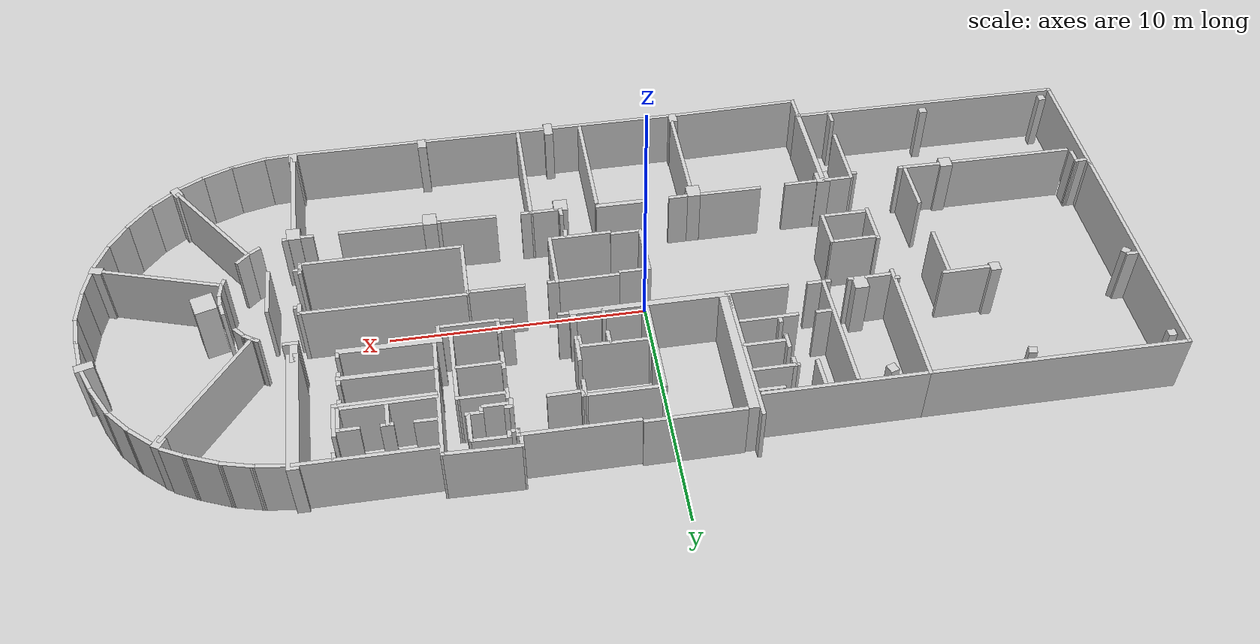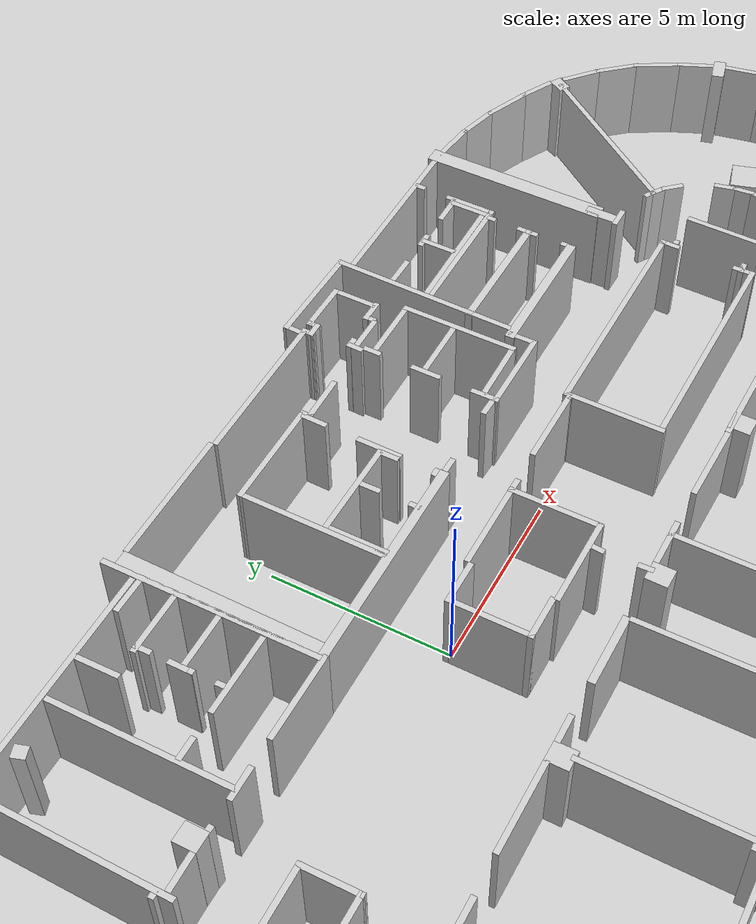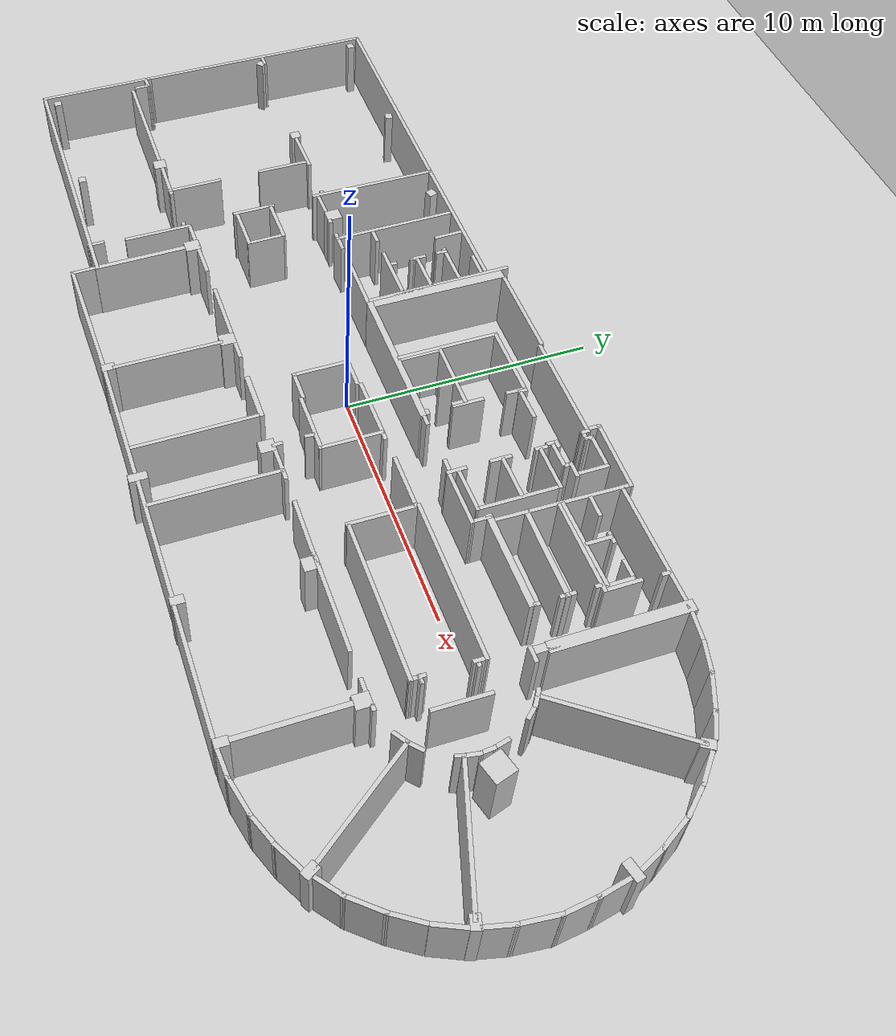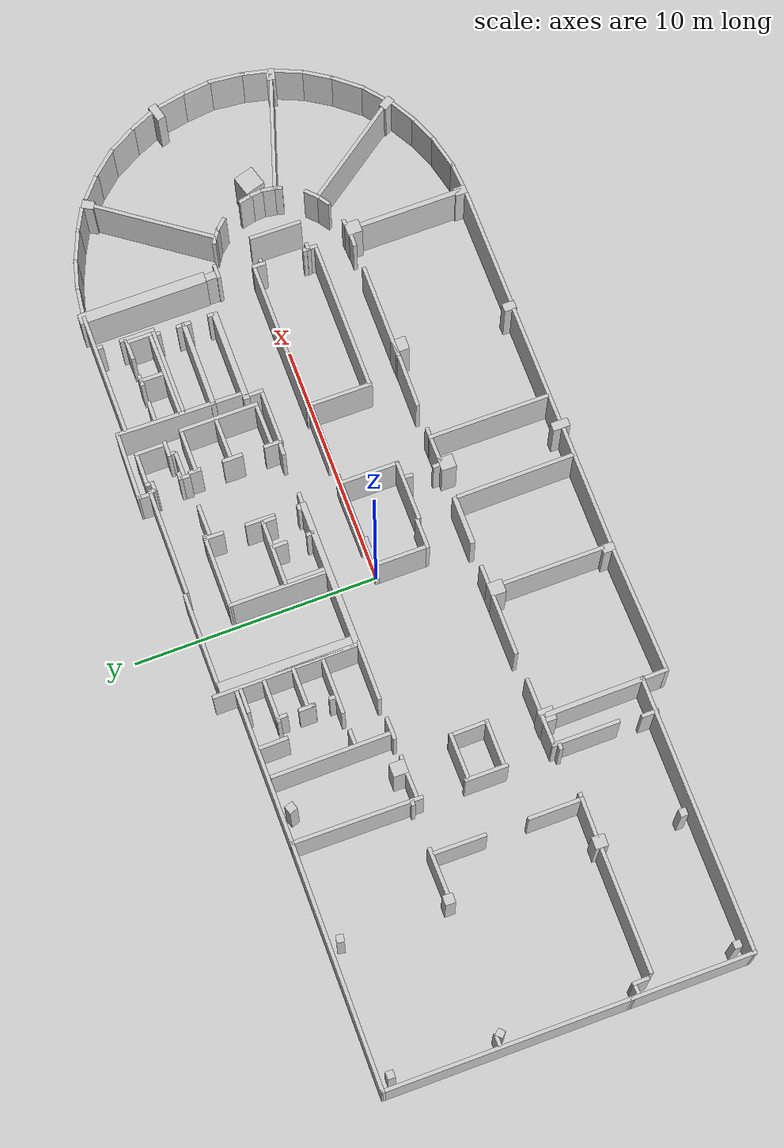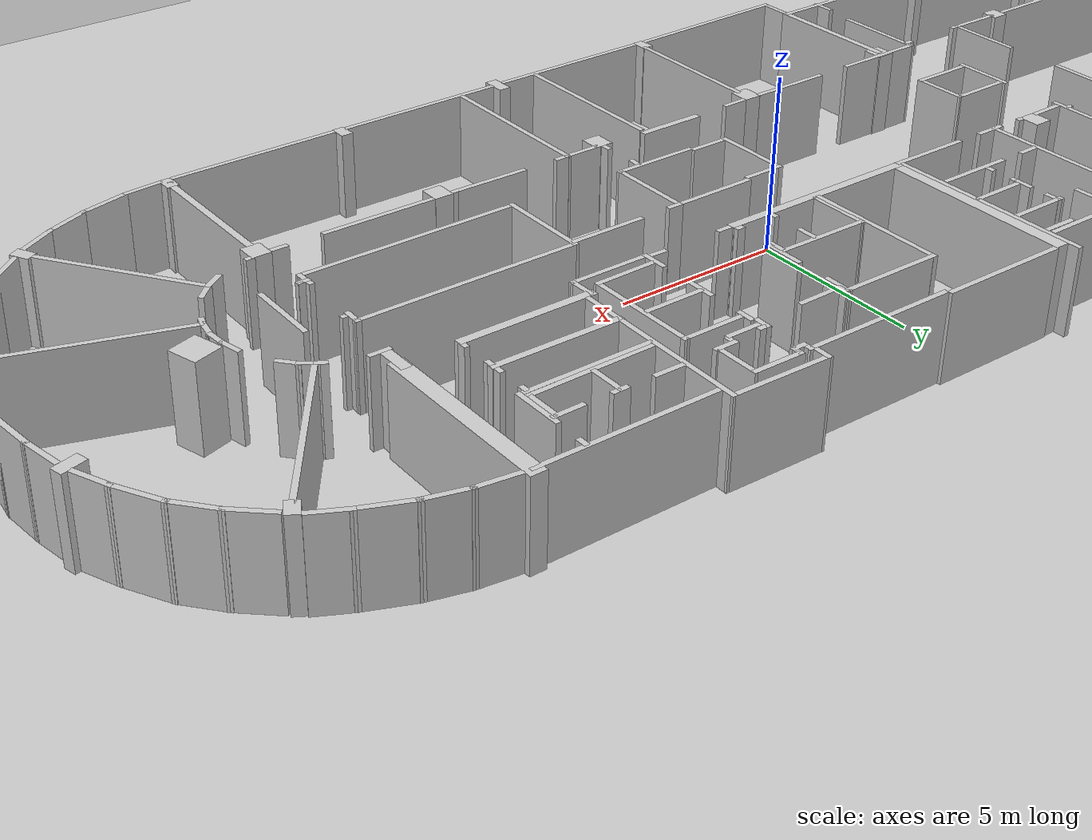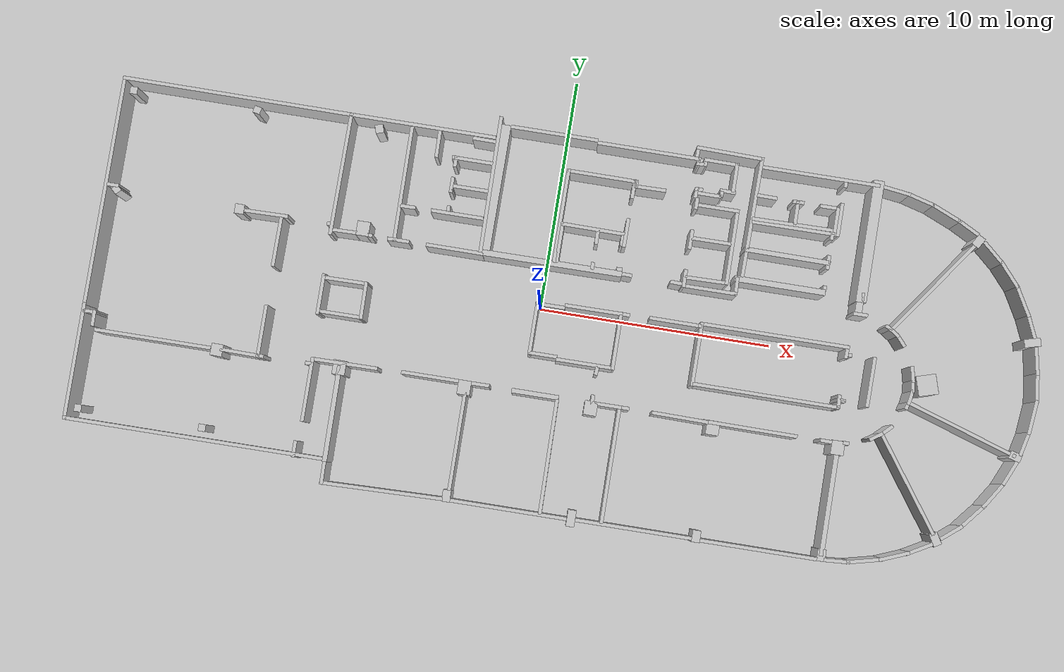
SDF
<?xml version="1.0" ?>

<sdf version="1.8">
  <world name="6OG">

    <gravity>0 0 -9.81</gravity>

    <light name="sun" type="directional">
      <cast_shadows>true</cast_shadows>
      <pose>0 0 10 0 0 0</pose>
      <diffuse>0.8 0.8 0.8 1</diffuse>
      <specular>0.2 0.2 0.2 1</specular>
      <attenuation>
        <range>1000</range>
        <constant>0.9</constant>
        <linear>0.01</linear>
        <quadratic>0.001</quadratic>
      </attenuation>
      <direction>-0.5 0.1 -0.9</direction>
    </light>

    <model name="ground_plane">
      <static>true</static>
      <link name="link">
        <collision name="collision">
          <geometry>
            <plane>
              <normal>0 0 1</normal>
              <size>1900 200</size>
            </plane>
          </geometry>
        </collision>
        <visual name="visual">
          <geometry>
            <plane>
              <normal>0 0 1</normal>
              <size>1900 200</size>
            </plane>
          </geometry>
          <material>
            <ambient>0.8 0.8 0.8 1</ambient>
            <diffuse>0.8 0.8 0.8 1</diffuse>
            <specular>0.8 0.8 0.8 1</specular>
          </material>
        </visual>
      </link>
    </model>

    <include>
      <uri>package://tiplu_world/models/6_OG_normal_doors</uri>
      <name>6_OG_normale_tueren</name>
    </include>

    <!-- TODO@Torben/Jacob: How do we pass a parameter into a sdf to distinguish between fortress and garden -->
  </world>
</sdf>

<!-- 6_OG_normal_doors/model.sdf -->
<sdf version='1.7'>
  <model name='New_6_OG_normale_tueren'>
  <!-- DOOR RELATED WALLS: 11, 15, 17, 23, 67, 71, 69, 343, 347 -->
    <pose>10.3487 -1.93317 0 0 -0 0</pose>
    <link name='Wall_101'>
      <collision name='Wall_101_Collision'>
        <geometry>
          <box>
            <size>1.67458 0.15 2.5</size>
          </box>
        </geometry>
        <pose>0 0 1.25 0 -0 0</pose>
      </collision>
      <visual name='Wall_101_Visual'>
        <pose>0 0 1.25 0 -0 0</pose>
        <geometry>
          <box>
            <size>1.67458 0.15 2.5</size>
          </box>
        </geometry>
        <material>
          <diffuse>0.8 0.8 0.8 1</diffuse>
          <specular>0.8 0.8 0.8 1</specular>
          <ambient>1 1 1 1</ambient>
        </material>
        <meta>
          <layer>0</layer>
        </meta>
      </visual>
      <pose>-22.5677 -2.0456 0 0 -0 -0.013157</pose>
    </link>
    <link name='Wall_103'>
      <collision name='Wall_103_Collision'>
        <geometry>
          <box>
            <size>0.272233 0.15 2.5</size>
          </box>
        </geometry>
        <pose>0.1 0 1.25 0 -0 0</pose>
      </collision>
      <visual name='Wall_103_Visual'>
        <pose>0.1 0 1.25 0 -0 0</pose>
        <geometry>
          <box>
            <size>0.272233 0.15 2.5</size>
          </box>
        </geometry>
        <material>
          <diffuse>0.8 0.8 0.8 1</diffuse>
          <specular>0.8 0.8 0.8 1</specular>
          <ambient>1 1 1 1</ambient>
        </material>
        <meta>
          <layer>0</layer>
        </meta>
      </visual>
      <pose>-19.7245 -2.0262 0 0 -0 0</pose>
    </link>
    <link name='Wall_105'>
      <collision name='Wall_105_Collision'>
        <geometry>
          <box>
            <size>2.25 0.15 2.5</size>
          </box>
        </geometry>
        <pose>0 0 1.25 0 -0 0</pose>
      </collision>
      <visual name='Wall_105_Visual'>
        <pose>0 0 1.25 0 -0 0</pose>
        <geometry>
          <box>
            <size>2.25 0.15 2.5</size>
          </box>
        </geometry>
        <material>
          <diffuse>0.8 0.8 0.8 1</diffuse>
          <specular>0.8 0.8 0.8 1</specular>
          <ambient>1 1 1 1</ambient>
        </material>
        <meta>
          <layer>0</layer>
        </meta>
      </visual>
      <pose>-21.7903 -1.00562 0 0 -0 1.5708</pose>
    </link>
    <link name='Wall_107'>
      <collision name='Wall_107_Collision'>
        <geometry>
          <box>
            <size>0.330367 0.15 2.5</size>
          </box>
        </geometry>
        <pose>0 0 1.25 0 -0 0</pose>
      </collision>
      <visual name='Wall_107_Visual'>
        <pose>0 0 1.25 0 -0 0</pose>
        <geometry>
          <box>
            <size>0.330367 0.15 2.5</size>
          </box>
        </geometry>
        <material>
          <diffuse>0.8 0.8 0.8 1</diffuse>
          <specular>0.8 0.8 0.8 1</specular>
          <ambient>1 1 1 1</ambient>
        </material>
        <meta>
          <layer>0</layer>
        </meta>
      </visual>
      <pose>-21.7001 -2.05463 0 0 -0 0.011083</pose>
    </link>
    <link name='Wall_109'>
      <collision name='Wall_109_Collision'>
        <geometry>
          <box>
            <size>2.12399 0.15 2.5</size>
          </box>
        </geometry>
        <pose>0 0 1.25 0 -0 0</pose>
      </collision>
      <visual name='Wall_109_Visual'>
        <pose>0 0 1.25 0 -0 0</pose>
        <geometry>
          <box>
            <size>2.12399 0.15 2.5</size>
          </box>
        </geometry>
        <material>
          <diffuse>0.8 0.8 0.8 1</diffuse>
          <specular>0.8 0.8 0.8 1</specular>
          <ambient>1 1 1 1</ambient>
        </material>
        <meta>
          <layer>0</layer>
        </meta>
      </visual>
      <pose>-21.7945 2.84097 0 0 -0 1.56199</pose>
    </link>
    <link name='Wall_11'>
      <collision name='Wall_11_Collision'>
        <geometry>
          <box>
             <size>2.75692 0.15 2.5</size>
          </box>
        </geometry>
        <pose>0 0 1.25 0 0 0</pose>
      </collision>
      <visual name='Wall_11_Visual'>
        <pose>0 0 1.25 0 0 0</pose>
        <geometry>
          <box>
            <size>2.75692 0.15 2.5</size>
          </box>
        </geometry>
        <material>
          <diffuse>0.8 0.8 0.8 1</diffuse>
          <specular>0.8 0.8 0.8 1</specular>
          <ambient>1 1 1 1</ambient>
        </material>
        <meta>
          <layer>0</layer>
        </meta>
      </visual>
      <pose>-18.0896 -1.80885 0 0 -0 0.006842</pose>
    </link>
    <link name='Wall_111'>
      <collision name='Wall_111_Collision'>
        <geometry>
          <box>
            <size>1.88436 0.15 2.5</size>
          </box>
        </geometry>
        <pose>0 0 1.25 0 -0 0</pose>
      </collision>
      <visual name='Wall_111_Visual'>
        <pose>0 0 1.25 0 -0 0</pose>
        <geometry>
          <box>
            <size>1.88436 0.15 2.5</size>
          </box>
        </geometry>
        <material>
          <diffuse>0.8 0.8 0.8 1</diffuse>
          <specular>0.8 0.8 0.8 1</specular>
          <ambient>1 1 1 1</ambient>
        </material>
        <meta>
          <layer>0</layer>
        </meta>
      </visual>
      <pose>-22.4578 3.95436 0 0 -0 -3.12616</pose>
    </link>
    <link name='Wall_113'>
      <collision name='Wall_113_Collision'>
        <geometry>
          <box>
            <size>5.27201 0.15 2.5</size>
          </box>
        </geometry>
        <pose>0 0 1.25 0 -0 0</pose>
      </collision>
      <visual name='Wall_113_Visual'>
        <pose>0 0 1.25 0 -0 0</pose>
        <geometry>
          <box>
            <size>5.27201 0.15 2.5</size>
          </box>
        </geometry>
        <material>
          <diffuse>0.8 0.8 0.8 1</diffuse>
          <specular>0.8 0.8 0.8 1</specular>
          <ambient>1 1 1 1</ambient>
        </material>
        <meta>
          <layer>0</layer>
        </meta>
      </visual>
      <pose>-19.6032 6.12793 0 0 -0 1.56061</pose>
    </link>
    <link name='Wall_115'>
      <collision name='Wall_115_Collision'>
        <geometry>
          <box>
            <size>0.205635 0.15 2.5</size>
          </box>
        </geometry>
        <pose>0 0 1.25 0 -0 0</pose>
      </collision>
      <visual name='Wall_115_Visual'>
        <pose>0 0 1.25 0 -0 0</pose>
        <geometry>
          <box>
            <size>0.205635 0.15 2.5</size>
          </box>
        </geometry>
        <material>
          <diffuse>0.8 0.8 0.8 1</diffuse>
          <specular>0.8 0.8 0.8 1</specular>
          <ambient>1 1 1 1</ambient>
        </material>
        <meta>
          <layer>0</layer>
        </meta>
      </visual>
      <pose>-19.7309 3.94996 0 0 -0 -0.010565</pose>
    </link>
    <link name='Wall_117'>
      <collision name='Wall_117_Collision'>
        <geometry>
          <box>
            <size>9.94018 0.15 2.5</size>
          </box>
        </geometry>
        <pose>0 0 1.25 0 -0 0</pose>
      </collision>
      <visual name='Wall_117_Visual'>
        <pose>0 0 1.25 0 -0 0</pose>
        <geometry>
          <box>
            <size>9.94018 0.15 2.5</size>
          </box>
        </geometry>
        <material>
          <diffuse>0.8 0.8 0.8 1</diffuse>
          <specular>0.8 0.8 0.8 1</specular>
          <ambient>1 1 1 1</ambient>
        </material>
        <meta>
          <layer>0</layer>
        </meta>
      </visual>
      <pose>-24.4721 8.71482 0 0 -0 -0.00354</pose>
    </link>
    <link name='Wall_120'>
      <collision name='Wall_120_Collision'>
        <geometry>
          <box>
            <size>0.232337 0.15 2.5</size>
          </box>
        </geometry>
        <pose>0 0 1.25 0 -0 0</pose>
      </collision>
      <visual name='Wall_120_Visual'>
        <pose>0 0 1.25 0 -0 0</pose>
        <geometry>
          <box>
            <size>0.232337 0.15 2.5</size>
          </box>
        </geometry>
        <material>
          <diffuse>0.8 0.8 0.8 1</diffuse>
          <specular>0.8 0.8 0.8 1</specular>
          <ambient>1 1 1 1</ambient>
        </material>
        <meta>
          <layer>0</layer>
        </meta>
      </visual>
      <pose>-17.9642 3.72928 0 0 -0 3.06898</pose>
    </link>
    <link name='Wall_122'>
      <collision name='Wall_122_Collision'>
        <geometry>
          <box>
            <size>1.03764 0.15 2.5</size>
          </box>
        </geometry>
        <pose>0 0 1.25 0 -0 0</pose>
      </collision>
      <visual name='Wall_122_Visual'>
        <pose>0 0 1.25 0 -0 0</pose>
        <geometry>
          <box>
            <size>1.03764 0.15 2.5</size>
          </box>
        </geometry>
        <material>
          <diffuse>0.8 0.8 0.8 1</diffuse>
          <specular>0.8 0.8 0.8 1</specular>
          <ambient>1 1 1 1</ambient>
        </material>
        <meta>
          <layer>0</layer>
        </meta>
      </visual>
      <pose>-19.0292 3.73228 0 0 -0 -3.12199</pose>
    </link>
    <link name='Wall_128'>
      <collision name='Wall_128_Collision'>
        <geometry>
          <box>
            <size>0.5 0.15 2.5</size>
          </box>
        </geometry>
        <pose>0 0 1.25 0 -0 0</pose>
      </collision>
      <visual name='Wall_128_Visual'>
        <pose>0 0 1.25 0 -0 0</pose>
        <geometry>
          <box>
            <size>0.5 0.15 2.5</size>
          </box>
        </geometry>
        <material>
          <diffuse>0.8 0.8 0.8 1</diffuse>
          <specular>0.8 0.8 0.8 1</specular>
          <ambient>1 1 1 1</ambient>
        </material>
        <meta>
          <layer>0</layer>
        </meta>
      </visual>
      <pose>-29.0803 4.12793 0 0 -0 0</pose>
    </link>
    <link name='Wall_13'>
      <collision name='Wall_13_Collision'>
        <geometry>
          <box>
            <size>2.47773 0.15 2.5</size>
          </box>
        </geometry>
        <pose>0 0 1.25 0 -0 0</pose>
      </collision>
      <visual name='Wall_13_Visual'>
        <pose>0 0 1.25 0 -0 0</pose>
        <geometry>
          <box>
            <size>2.47773 0.15 2.5</size>
          </box>
        </geometry>
        <material>
          <diffuse>0.8 0.8 0.8 1</diffuse>
          <specular>0.8 0.8 0.8 1</specular>
          <ambient>1 1 1 1</ambient>
        </material>
        <meta>
          <layer>0</layer>
        </meta>
      </visual>
      <pose>-14.4542 -1.77144 0 0 -0 0.000874</pose>
    </link>
    <link name='Wall_130'>
      <collision name='Wall_130_Collision'>
        <geometry>
          <box>
            <size>0.929146 0.15 2.5</size>
          </box>
        </geometry>
        <pose>0 0 1.25 0 -0 0</pose>
      </collision>
      <visual name='Wall_130_Visual'>
        <pose>0 0 1.25 0 -0 0</pose>
        <geometry>
          <box>
            <size>0.929146 0.15 2.5</size>
          </box>
        </geometry>
        <material>
          <diffuse>0.8 0.8 0.8 1</diffuse>
          <specular>0.8 0.8 0.8 1</specular>
          <ambient>1 1 1 1</ambient>
        </material>
        <meta>
          <layer>0</layer>
        </meta>
      </visual>
      <pose>-16.7342 3.71479 0 0 -0 0.00738</pose>
    </link>
    <link name='Wall_133'>
      <collision name='Wall_133_Collision'>
        <geometry>
          <box>
            <size>4.96069 0.15 2.5</size>
          </box>
        </geometry>
        <pose>0 0 1.25 0 -0 0</pose>
      </collision>
      <visual name='Wall_133_Visual'>
        <pose>0 0 1.25 0 -0 0</pose>
        <geometry>
          <box>
            <size>4.96069 0.15 2.5</size>
          </box>
        </geometry>
        <material>
          <diffuse>0.8 0.8 0.8 1</diffuse>
          <specular>0.8 0.8 0.8 1</specular>
          <ambient>1 1 1 1</ambient>
        </material>
        <meta>
          <layer>0</layer>
        </meta>
      </visual>
      <pose>-16.9219 6.12446 0 0 -0 -1.56443</pose>
    </link>
    <link name='Wall_135'>
      <collision name='Wall_135_Collision'>
        <geometry>
          <box>
            <size>6.30443 0.15 2.5</size>
          </box>
        </geometry>
        <pose>0 0 1.25 0 -0 0</pose>
      </collision>
      <visual name='Wall_135_Visual'>
        <pose>0 0 1.25 0 -0 0</pose>
        <geometry>
          <box>
            <size>6.30443 0.15 2.5</size>
          </box>
        </geometry>
        <material>
          <diffuse>0.8 0.8 0.8 1</diffuse>
          <specular>0.8 0.8 0.8 1</specular>
          <ambient>1 1 1 1</ambient>
        </material>
        <meta>
          <layer>0</layer>
        </meta>
      </visual>
      <pose>-16.4999 8.69565 0 0 -0 -0.000599</pose>
    </link>
    <link name='Wall_138'>
      <collision name='Wall_138_Collision'>
        <geometry>
          <box>
            <size>0.989569 0.15 2.5</size>
          </box>
        </geometry>
        <pose>0 0 1.25 0 -0 0</pose>
      </collision>
      <visual name='Wall_138_Visual'>
        <pose>0 0 1.25 0 -0 0</pose>
        <geometry>
          <box>
            <size>0.989569 0.15 2.5</size>
          </box>
        </geometry>
        <material>
          <diffuse>0.8 0.8 0.8 1</diffuse>
          <specular>0.8 0.8 0.8 1</specular>
          <ambient>1 1 1 1</ambient>
        </material>
        <meta>
          <layer>0</layer>
        </meta>
      </visual>
      <pose>-13.8162 8.52328 0 0 -0 3.13118</pose>
    </link>
    <link name='Wall_141'>
      <collision name='Wall_141_Collision'>
        <geometry>
          <box>
            <size>1.75 0.15 2.5</size>
          </box>
        </geometry>
        <pose>0 0 1.25 0 -0 0</pose>
      </collision>
      <visual name='Wall_141_Visual'>
        <pose>0 0 1.25 0 -0 0</pose>
        <geometry>
          <box>
            <size>1.75 0.15 2.5</size>
          </box>
        </geometry>
        <material>
          <diffuse>0.8 0.8 0.8 1</diffuse>
          <specular>0.8 0.8 0.8 1</specular>
          <ambient>1 1 1 1</ambient>
        </material>
        <meta>
          <layer>0</layer>
        </meta>
      </visual>
      <pose>-14.1793 7.57444 0 0 -0 0</pose>
    </link>
    <link name='Wall_143'>
      <collision name='Wall_143_Collision'>
        <geometry>
          <box>
            <size>1.18206 0.15 2.5</size>
          </box>
        </geometry>
        <pose>0 0 1.25 0 -0 0</pose>
      </collision>
      <visual name='Wall_143_Visual'>
        <pose>0 0 1.25 0 -0 0</pose>
        <geometry>
          <box>
            <size>1.18206 0.15 2.5</size>
          </box>
        </geometry>
        <material>
          <diffuse>0.8 0.8 0.8 1</diffuse>
          <specular>0.8 0.8 0.8 1</specular>
          <ambient>1 1 1 1</ambient>
        </material>
        <meta>
          <layer>0</layer>
        </meta>
      </visual>
      <pose>-15.7313 8.05542 0 0 -0 1.58774</pose>
    </link>
    <link name='Wall_147'>
      <collision name='Wall_147_Collision'>
        <geometry>
          <box>
            <size>5.86345 0.15 2.5</size>
          </box>
        </geometry>
        <pose>0 0 1.25 0 -0 0</pose>
      </collision>
      <visual name='Wall_147_Visual'>
        <pose>0 0 1.25 0 -0 0</pose>
        <geometry>
          <box>
            <size>5.86345 0.15 2.5</size>
          </box>
        </geometry>
        <material>
          <diffuse>0.8 0.8 0.8 1</diffuse>
          <specular>0.8 0.8 0.8 1</specular>
          <ambient>1 1 1 1</ambient>
        </material>
        <meta>
          <layer>0</layer>
        </meta>
      </visual>
      <pose>-13.2445 6.69415 0 0 -0 -1.56353</pose>
    </link>
    <link name='Wall_149'>
      <collision name='Wall_149_Collision'>
        <geometry>
          <box>
            <size>2.44907 0.15 2.5</size>
          </box>
        </geometry>
        <pose>0 0 1.25 0 -0 0</pose>
      </collision>
      <visual name='Wall_149_Visual'>
        <pose>0 0 1.25 0 -0 0</pose>
        <geometry>
          <box>
            <size>2.44907 0.15 2.5</size>
          </box>
        </geometry>
        <material>
          <diffuse>0.8 0.8 0.8 1</diffuse>
          <specular>0.8 0.8 0.8 1</specular>
          <ambient>1 1 1 1</ambient>
        </material>
        <meta>
          <layer>0</layer>
        </meta>
      </visual>
      <pose>-14.3183 3.71507 0 0 -0 -0.002254</pose>
    </link>
    <link name='Wall_15'>
      <collision name='Wall_15_Collision'>
        <geometry>
          <box>
            <size>0.776555 0.15 2.5</size>
          </box>
        </geometry>
        <pose>0 0 1.25 0 0 0</pose>
      </collision>
      <visual name='Wall_15_Visual'>
        <pose>0 0 1.25 0 0 0</pose>
        <geometry>
          <box>
            <size>0.776555 0.15 2.5</size>
          </box>
        </geometry>
        <material>
          <diffuse>0.8 0.8 0.8 1</diffuse>
          <specular>0.8 0.8 0.8 1</specular>
          <ambient>1 1 1 1</ambient>
        </material>
        <meta>
          <layer>0</layer>
        </meta>
      </visual>
      <pose>-12.3227 -1.77109 0 0 -0 0.00822</pose>
    </link>
    <link name='Wall_152'>
      <collision name='Wall_152_Collision'>
        <geometry>
          <box>
            <size>0.438918 0.15 2.5</size>
          </box>
        </geometry>
        <pose>0 0 1.25 0 -0 0</pose>
      </collision>
      <visual name='Wall_152_Visual'>
        <pose>0 0 1.25 0 -0 0</pose>
        <geometry>
          <box>
            <size>0.438918 0.15 2.5</size>
          </box>
        </geometry>
        <material>
          <diffuse>0.8 0.8 0.8 1</diffuse>
          <specular>0.8 0.8 0.8 1</specular>
          <ambient>1 1 1 1</ambient>
        </material>
        <meta>
          <layer>0</layer>
        </meta>
      </visual>
      <pose>-6.9393 3.79409 0 0 -0 3.12331</pose>
    </link>
    <link name='Wall_154'>
      <collision name='Wall_154_Collision'>
        <geometry>
          <box>
            <size>5.9975 0.25 2.5</size>
          </box>
        </geometry>
        <pose>0 0 1.25 0 -0 0</pose>
      </collision>
      <visual name='Wall_154_Visual'>
        <pose>0 0 1.25 0 -0 0</pose>
        <geometry>
          <box>
            <size>5.9975 0.25 2.5</size>
          </box>
        </geometry>
        <material>
          <diffuse>0.8 0.8 0.8 1</diffuse>
          <specular>0.8 0.8 0.8 1</specular>
          <ambient>1 1 1 1</ambient>
        </material>
        <meta>
          <layer>0</layer>
        </meta>
      </visual>
      <pose>-10.1575 3.77921 0 0 -0 -3.13871</pose>
    </link>
    <link name='Wall_158'>
      <collision name='Wall_158_Collision'>
        <geometry>
          <box>
            <size>5.40653 0.4 2.5</size>
          </box>
        </geometry>
        <pose>0 0 1.25 0 -0 0</pose>
      </collision>
      <visual name='Wall_158_Visual'>
        <pose>0 0 1.25 0 -0 0</pose>
        <geometry>
          <box>
            <size>5.40653 0.4 2.5</size>
          </box>
        </geometry>
        <material>
          <diffuse>0.8 0.8 0.8 1</diffuse>
          <specular>0.8 0.8 0.8 1</specular>
          <ambient>1 1 1 1</ambient>
        </material>
        <meta>
          <layer>0</layer>
        </meta>
      </visual>
      <pose>-13.0102 6.59567 0 0 -0 -1.57821</pose>
    </link>
    <link name='Wall_162'>
      <collision name='Wall_162_Collision'>
        <geometry>
          <box>
            <size>3.75 0.15 2.5</size>
          </box>
        </geometry>
        <pose>0 0 1.25 0 -0 0</pose>
      </collision>
      <visual name='Wall_162_Visual'>
        <pose>0 0 1.25 0 -0 0</pose>
        <geometry>
          <box>
            <size>3.75 0.15 2.5</size>
          </box>
        </geometry>
        <material>
          <diffuse>0.8 0.8 0.8 1</diffuse>
          <specular>0.8 0.8 0.8 1</specular>
          <ambient>1 1 1 1</ambient>
        </material>
        <meta>
          <layer>0</layer>
        </meta>
      </visual>
      <pose>-10.9184 9.26341 0 0 -0 3.14159</pose>
    </link>
    <link name='Wall_164'>
      <collision name='Wall_164_Collision'>
        <geometry>
          <box>
            <size>3.00696 0.15 2.5</size>
          </box>
        </geometry>
        <pose>0 0 1.25 0 -0 0</pose>
      </collision>
      <visual name='Wall_164_Visual'>
        <pose>0 0 1.25 0 -0 0</pose>
        <geometry>
          <box>
            <size>3.00696 0.15 2.5</size>
          </box>
        </geometry>
        <material>
          <diffuse>0.8 0.8 0.8 1</diffuse>
          <specular>0.8 0.8 0.8 1</specular>
          <ambient>1 1 1 1</ambient>
        </material>
        <meta>
          <layer>0</layer>
        </meta>
      </visual>
      <pose>-8.64761 7.78528 0 0 -0 -0.002915</pose>
    </link>
    <link name='Wall_166'>
      <collision name='Wall_166_Collision'>
        <geometry>
          <box>
            <size>1.23115 0.15 2.5</size>
          </box>
        </geometry>
        <pose>0 0 1.25 0 -0 0</pose>
      </collision>
      <visual name='Wall_166_Visual'>
        <pose>0 0 1.25 0 -0 0</pose>
        <geometry>
          <box>
            <size>1.23115 0.15 2.5</size>
          </box>
        </geometry>
        <material>
          <diffuse>0.8 0.8 0.8 1</diffuse>
          <specular>0.8 0.8 0.8 1</specular>
          <ambient>1 1 1 1</ambient>
        </material>
        <meta>
          <layer>0</layer>
        </meta>
      </visual>
      <pose>-7.25141 5.55807 0 0 -0 1.56079</pose>
    </link>
    <link name='Wall_168'>
      <collision name='Wall_168_Collision'>
        <geometry>
          <box>
            <size>0.808489 0.15 2.5</size>
          </box>
        </geometry>
        <pose>0 0 1.25 0 -0 0</pose>
      </collision>
      <visual name='Wall_168_Visual'>
        <pose>0 0 1.25 0 -0 0</pose>
        <geometry>
          <box>
            <size>0.808489 0.15 2.5</size>
          </box>
        </geometry>
        <material>
          <diffuse>0.8 0.8 0.8 1</diffuse>
          <specular>0.8 0.8 0.8 1</specular>
          <ambient>1 1 1 1</ambient>
        </material>
        <meta>
          <layer>0</layer>
        </meta>
      </visual>
      <pose>-7.22578 7.45194 0 0 -0 1.5506</pose>
    </link>
    <link name='Wall_17'>
      <collision name='Wall_17_Collision'>
        <geometry>
          <box>
            <size>2 0.2 2.5</size>
          </box>
        </geometry>
        <pose>0 0 1.2 0 -0 0</pose>
      </collision>
      <visual name='Wall_17_Visual'>
        <pose>0 0 1.2 0 -0 0</pose>
        <geometry>
          <box>
            <size>2 0.2 2.5</size>
          </box>
        </geometry>
        <material>
          <diffuse>0.8 0.8 0.8 1</diffuse>
          <specular>0.8 0.8 0.8 1</specular>
          <ambient>1 1 1 1</ambient>
        </material>
        <meta>
          <layer>0</layer>
        </meta>
      </visual>
      <pose>-9.97809 -1.79869 0 0 -0 0</pose>
    </link>
    <link name='Wall_170'>
      <collision name='Wall_170_Collision'>
        <geometry>
          <box>
            <size>4.03895 0.15 2.5</size>
          </box>
        </geometry>
        <pose>0 0 1.25 0 -0 0</pose>
      </collision>
      <visual name='Wall_170_Visual'>
        <pose>0 0 1.25 0 -0 0</pose>
        <geometry>
          <box>
            <size>4.03895 0.15 2.5</size>
          </box>
        </geometry>
        <material>
          <diffuse>0.8 0.8 0.8 1</diffuse>
          <specular>0.8 0.8 0.8 1</specular>
          <ambient>1 1 1 1</ambient>
        </material>
        <meta>
          <layer>0</layer>
        </meta>
      </visual>
      <pose>-10.0794 5.85162 0 0 -0 -1.57251</pose>
    </link>
    <link name='Wall_172'>
      <collision name='Wall_172_Collision'>
        <geometry>
          <box>
            <size>2.75013 0.15 2.5</size>
          </box>
        </geometry>
        <pose>0 0 1.25 0 -0 0</pose>
      </collision>
      <visual name='Wall_172_Visual'>
        <pose>0 0 1.25 0 -0 0</pose>
        <geometry>
          <box>
            <size>2.75013 0.15 2.5</size>
          </box>
        </geometry>
        <material>
          <diffuse>0.8 0.8 0.8 1</diffuse>
          <specular>0.8 0.8 0.8 1</specular>
          <ambient>1 1 1 1</ambient>
        </material>
        <meta>
          <layer>0</layer>
        </meta>
      </visual>
      <pose>-8.667 5.4928 0 0 -0 -0.01009</pose>
    </link>
    <link name='Wall_174'>
      <collision name='Wall_174_Collision'>
        <geometry>
          <box>
            <size>1.75 0.15 2.5</size>
          </box>
        </geometry>
        <pose>0 0 1.25 0 -0 0</pose>
      </collision>
      <visual name='Wall_174_Visual'>
        <pose>0 0 1.25 0 -0 0</pose>
        <geometry>
          <box>
            <size>1.75 0.15 2.5</size>
          </box>
        </geometry>
        <material>
          <diffuse>0.8 0.8 0.8 1</diffuse>
          <specular>0.8 0.8 0.8 1</specular>
          <ambient>1 1 1 1</ambient>
        </material>
        <meta>
          <layer>0</layer>
        </meta>
      </visual>
      <pose>-9.967 4.70592 0 0 -0 -1.5708</pose>
    </link>
    <link name='Wall_176'>
      <collision name='Wall_176_Collision'>
        <geometry>
          <box>
            <size>0.602751 0.15 2.5</size>
          </box>
        </geometry>
        <pose>0 0 1.25 0 -0 0</pose>
      </collision>
      <visual name='Wall_176_Visual'>
        <pose>0 0 1.25 0 -0 0</pose>
        <geometry>
          <box>
            <size>0.602751 0.15 2.5</size>
          </box>
        </geometry>
        <material>
          <diffuse>0.8 0.8 0.8 1</diffuse>
          <specular>0.8 0.8 0.8 1</specular>
          <ambient>1 1 1 1</ambient>
        </material>
        <meta>
          <layer>0</layer>
        </meta>
      </visual>
      <pose>-8.44182 5.17566 0 0 -0 -1.56317</pose>
    </link>
    <link name='Wall_178'>
      <collision name='Wall_178_Collision'>
        <geometry>
          <box>
            <size>0.303038 0.15 2.5</size>
          </box>
        </geometry>
        <pose>0 0 1.25 0 -0 0</pose>
      </collision>
      <visual name='Wall_178_Visual'>
        <pose>0 0 1.25 0 -0 0</pose>
        <geometry>
          <box>
            <size>0.303038 0.15 2.5</size>
          </box>
        </geometry>
        <material>
          <diffuse>0.8 0.8 0.8 1</diffuse>
          <specular>0.8 0.8 0.8 1</specular>
          <ambient>1 1 1 1</ambient>
        </material>
        <meta>
          <layer>0</layer>
        </meta>
      </visual>
      <pose>-8.43752 3.94317 0 0 -0 -1.5708</pose>
    </link>
    <link name='Wall_184'>
      <collision name='Wall_184_Collision'>
        <geometry>
          <box>
            <size>0.5 0.15 2.5</size>
          </box>
        </geometry>
        <pose>0 0 1.25 0 -0 0</pose>
      </collision>
      <visual name='Wall_184_Visual'>
        <pose>0 0 1.25 0 -0 0</pose>
        <geometry>
          <box>
            <size>0.5 0.15 2.5</size>
          </box>
        </geometry>
        <material>
          <diffuse>0.8 0.8 0.8 1</diffuse>
          <specular>0.8 0.8 0.8 1</specular>
          <ambient>1 1 1 1</ambient>
        </material>
        <meta>
          <layer>0</layer>
        </meta>
      </visual>
      <pose>-7.36175 5.2101 0 0 -0 -1.5708</pose>
    </link>
    <link name='Wall_188'>
      <collision name='Wall_188_Collision'>
        <geometry>
          <box>
            <size>0.25 0.15 2.5</size>
          </box>
        </geometry>
        <pose>0 0 1.25 0 -0 0</pose>
      </collision>
      <visual name='Wall_188_Visual'>
        <pose>0 0 1.25 0 -0 0</pose>
        <geometry>
          <box>
            <size>0.25 0.15 2.5</size>
          </box>
        </geometry>
        <material>
          <diffuse>0.8 0.8 0.8 1</diffuse>
          <specular>0.8 0.8 0.8 1</specular>
          <ambient>1 1 1 1</ambient>
        </material>
        <meta>
          <layer>0</layer>
        </meta>
      </visual>
      <pose>-7.29427 3.97715 0 0 -0 0</pose>
    </link>
    <link name='Wall_19'>
      <collision name='Wall_19_Collision'>
        <geometry>
          <box>
            <size>1.15349 0.15 2.5</size>
          </box>
        </geometry>
        <pose>0 0 1.25 0 -0 0</pose>
      </collision>
      <visual name='Wall_19_Visual'>
        <pose>0 0 1.25 0 -0 0</pose>
        <geometry>
          <box>
            <size>1.15349 0.15 2.5</size>
          </box>
        </geometry>
        <material>
          <diffuse>0.8 0.8 0.8 1</diffuse>
          <specular>0.8 0.8 0.8 1</specular>
          <ambient>1 1 1 1</ambient>
        </material>
        <meta>
          <layer>0</layer>
        </meta>
      </visual>
      <pose>-6.87291 -1.78985 0 0 -0 -3.13714</pose>
    </link>
    <link name='Wall_190'>
      <collision name='Wall_190_Collision'>
        <geometry>
          <box>
            <size>0.500143 0.15 2.5</size>
          </box>
        </geometry>
        <pose>0 0 1.25 0 -0 0</pose>
      </collision>
      <visual name='Wall_190_Visual'>
        <pose>0 0 1.25 0 -0 0</pose>
        <geometry>
          <box>
            <size>0.500143 0.15 2.5</size>
          </box>
        </geometry>
        <material>
          <diffuse>0.8 0.8 0.8 1</diffuse>
          <specular>0.8 0.8 0.8 1</specular>
          <ambient>1 1 1 1</ambient>
        </material>
        <meta>
          <layer>0</layer>
        </meta>
      </visual>
      <pose>-4.82652 3.79067 0 0 -0 -0.028564</pose>
    </link>
    <link name='Wall_192'>
      <collision name='Wall_192_Collision'>
        <geometry>
          <box>
            <size>0.773976 0.15 2.5</size>
          </box>
        </geometry>
        <pose>0 0 1.25 0 -0 0</pose>
      </collision>
      <visual name='Wall_192_Visual'>
        <pose>0 0 1.25 0 -0 0</pose>
        <geometry>
          <box>
            <size>0.773976 0.15 2.5</size>
          </box>
        </geometry>
        <material>
          <diffuse>0.8 0.8 0.8 1</diffuse>
          <specular>0.8 0.8 0.8 1</specular>
          <ambient>1 1 1 1</ambient>
        </material>
        <meta>
          <layer>0</layer>
        </meta>
      </visual>
      <pose>-4.50076 4.0341 0 0 -0 -1.5586</pose>
    </link>
    <link name='Wall_194'>
      <collision name='Wall_194_Collision'>
        <geometry>
          <box>
            <size>2.36359 0.15 2.5</size>
          </box>
        </geometry>
        <pose>0 0 1.25 0 -0 0</pose>
      </collision>
      <visual name='Wall_194_Visual'>
        <pose>0 0 1.25 0 -0 0</pose>
        <geometry>
          <box>
            <size>2.36359 0.15 2.5</size>
          </box>
        </geometry>
        <material>
          <diffuse>0.8 0.8 0.8 1</diffuse>
          <specular>0.8 0.8 0.8 1</specular>
          <ambient>1 1 1 1</ambient>
        </material>
        <meta>
          <layer>0</layer>
        </meta>
      </visual>
      <pose>-3.39021 3.72482 0 0 -0 -3.13933</pose>
    </link>
    <link name='Wall_196'>
      <collision name='Wall_196_Collision'>
        <geometry>
          <box>
            <size>0.834394 0.15 2.5</size>
          </box>
        </geometry>
        <pose>0 0 1.25 0 -0 0</pose>
      </collision>
      <visual name='Wall_196_Visual'>
        <pose>0 0 1.25 0 -0 0</pose>
        <geometry>
          <box>
            <size>0.834394 0.15 2.5</size>
          </box>
        </geometry>
        <material>
          <diffuse>0.8 0.8 0.8 1</diffuse>
          <specular>0.8 0.8 0.8 1</specular>
          <ambient>1 1 1 1</ambient>
        </material>
        <meta>
          <layer>0</layer>
        </meta>
      </visual>
      <pose>-4.49696 5.71467 0 0 -0 -1.5708</pose>
    </link>
    <link name='Wall_199'>
      <collision name='Wall_199_Collision'>
        <geometry>
          <box>
            <size>1.26849 0.15 2.5</size>
          </box>
        </geometry>
        <pose>0 0 1.25 0 -0 0</pose>
      </collision>
      <visual name='Wall_199_Visual'>
        <pose>0 0 1.25 0 -0 0</pose>
        <geometry>
          <box>
            <size>1.26849 0.15 2.5</size>
          </box>
        </geometry>
        <material>
          <diffuse>0.8 0.8 0.8 1</diffuse>
          <specular>0.8 0.8 0.8 1</specular>
          <ambient>1 1 1 1</ambient>
        </material>
        <meta>
          <layer>0</layer>
        </meta>
      </visual>
      <pose>-6.4931 7.58534 0 0 -0 -3.12799</pose>
    </link>
    <link name='Wall_205'>
      <collision name='Wall_205_Collision'>
        <geometry>
          <box>
            <size>4.43127 0.15 2.5</size>
          </box>
        </geometry>
        <pose>0 0 1.25 0 -0 0</pose>
      </collision>
      <visual name='Wall_205_Visual'>
        <pose>0 0 1.25 0 -0 0</pose>
        <geometry>
          <box>
            <size>4.43127 0.15 2.5</size>
          </box>
        </geometry>
        <material>
          <diffuse>0.8 0.8 0.8 1</diffuse>
          <specular>0.8 0.8 0.8 1</specular>
          <ambient>1 1 1 1</ambient>
        </material>
        <meta>
          <layer>0</layer>
        </meta>
      </visual>
      <pose>-6.8277 9.16325 0 0 -0 3.13982</pose>
    </link>
    <link name='Wall_207'>
      <collision name='Wall_207_Collision'>
        <geometry>
          <box>
            <size>0.355881 0.15 2.5</size>
          </box>
        </geometry>
        <pose>0 0 1.25 0 -0 0</pose>
      </collision>
      <visual name='Wall_207_Visual'>
        <pose>0 0 1.25 0 -0 0</pose>
        <geometry>
          <box>
            <size>0.355881 0.15 2.5</size>
          </box>
        </geometry>
        <material>
          <diffuse>0.8 0.8 0.8 1</diffuse>
          <specular>0.8 0.8 0.8 1</specular>
          <ambient>1 1 1 1</ambient>
        </material>
        <meta>
          <layer>0</layer>
        </meta>
      </visual>
      <pose>-4.68707 9.05679 0 0 -0 -1.5708</pose>
    </link>
    <link name='Wall_208'>
      <collision name='Wall_208_Collision'>
        <geometry>
          <box>
            <size>0.455029 0.15 2.5</size>
          </box>
        </geometry>
        <pose>0 0 1.25 0 -0 0</pose>
      </collision>
      <visual name='Wall_208_Visual'>
        <pose>0 0 1.25 0 -0 0</pose>
        <geometry>
          <box>
            <size>0.455029 0.15 2.5</size>
          </box>
        </geometry>
        <material>
          <diffuse>0.8 0.8 0.8 1</diffuse>
          <specular>0.8 0.8 0.8 1</specular>
          <ambient>1 1 1 1</ambient>
        </material>
        <meta>
          <layer>0</layer>
        </meta>
      </visual>
      <pose>-4.53498 8.95793 0 0 -0 0.024995</pose>
    </link>
    <link name='Wall_209'>
      <collision name='Wall_209_Collision'>
        <geometry>
          <box>
            <size>0.355318 0.15 2.5</size>
          </box>
        </geometry>
        <pose>0 0 1.25 0 -0 0</pose>
      </collision>
      <visual name='Wall_209_Visual'>
        <pose>0 0 1.25 0 -0 0</pose>
        <geometry>
          <box>
            <size>0.355318 0.15 2.5</size>
          </box>
        </geometry>
        <material>
          <diffuse>0.8 0.8 0.8 1</diffuse>
          <specular>0.8 0.8 0.8 1</specular>
          <ambient>1 1 1 1</ambient>
        </material>
        <meta>
          <layer>0</layer>
        </meta>
      </visual>
      <pose>-4.38289 9.06439 0 0 -0 1.5708</pose>
    </link>
    <link name='Wall_210'>
      <collision name='Wall_210_Collision'>
        <geometry>
          <box>
            <size>1.48085 0.15 2.5</size>
          </box>
        </geometry>
        <pose>0 0 1.25 0 -0 0</pose>
      </collision>
      <visual name='Wall_210_Visual'>
        <pose>0 0 1.25 0 -0 0</pose>
        <geometry>
          <box>
            <size>1.48085 0.15 2.5</size>
          </box>
        </geometry>
        <material>
          <diffuse>0.8 0.8 0.8 1</diffuse>
          <specular>0.8 0.8 0.8 1</specular>
          <ambient>1 1 1 1</ambient>
        </material>
        <meta>
          <layer>0</layer>
        </meta>
      </visual>
      <pose>-3.71751 9.16705 0 0 -0 -0.011428</pose>
    </link>
    <link name='Wall_212'>
      <collision name='Wall_212_Collision'>
        <geometry>
          <box>
            <size>1.25 0.15 2.5</size>
          </box>
        </geometry>
        <pose>0 0 1.25 0 -0 0</pose>
      </collision>
      <visual name='Wall_212_Visual'>
        <pose>0 0 1.25 0 -0 0</pose>
        <geometry>
          <box>
            <size>1.25 0.15 2.5</size>
          </box>
        </geometry>
        <material>
          <diffuse>0.8 0.8 0.8 1</diffuse>
          <specular>0.8 0.8 0.8 1</specular>
          <ambient>1 1 1 1</ambient>
        </material>
        <meta>
          <layer>0</layer>
        </meta>
      </visual>
      <pose>-3.04452 8.60945 0 0 -0 -1.5708</pose>
    </link>
    <link name='Wall_214'>
      <collision name='Wall_214_Collision'>
        <geometry>
          <box>
            <size>0.459849 0.15 2.5</size>
          </box>
        </geometry>
        <pose>0 0 1.25 0 -0 0</pose>
      </collision>
      <visual name='Wall_214_Visual'>
        <pose>0 0 1.25 0 -0 0</pose>
        <geometry>
          <box>
            <size>0.459849 0.15 2.5</size>
          </box>
        </geometry>
        <material>
          <diffuse>0.8 0.8 0.8 1</diffuse>
          <specular>0.8 0.8 0.8 1</specular>
          <ambient>1 1 1 1</ambient>
        </material>
        <meta>
          <layer>0</layer>
        </meta>
      </visual>
      <pose>-4.58191 7.72493 0 0 -0 -1.61149</pose>
    </link>
    <link name='Wall_216'>
      <collision name='Wall_216_Collision'>
        <geometry>
          <box>
            <size>0.340261 0.15 2.5</size>
          </box>
        </geometry>
        <pose>0 0 1.25 0 -0 0</pose>
      </collision>
      <visual name='Wall_216_Visual'>
        <pose>0 0 1.25 0 -0 0</pose>
        <geometry>
          <box>
            <size>0.340261 0.15 2.5</size>
          </box>
        </geometry>
        <material>
          <diffuse>0.8 0.8 0.8 1</diffuse>
          <specular>0.8 0.8 0.8 1</specular>
          <ambient>1 1 1 1</ambient>
        </material>
        <meta>
          <layer>0</layer>
        </meta>
      </visual>
      <pose>-4.48555 7.87593 0 0 -0 -0.039979</pose>
    </link>
    <link name='Wall_218'>
      <collision name='Wall_218_Collision'>
        <geometry>
          <box>
            <size>1 0.15 2.5</size>
          </box>
        </geometry>
        <pose>0 0 1.25 0 -0 0</pose>
      </collision>
      <visual name='Wall_218_Visual'>
        <pose>0 0 1.25 0 -0 0</pose>
        <geometry>
          <box>
            <size>1 0.15 2.5</size>
          </box>
        </geometry>
        <material>
          <diffuse>0.8 0.8 0.8 1</diffuse>
          <specular>0.8 0.8 0.8 1</specular>
          <ambient>1 1 1 1</ambient>
        </material>
        <meta>
          <layer>0</layer>
        </meta>
      </visual>
      <pose>-4.01704 7.71224 0 0 -0 3.14159</pose>
    </link>
    <link name='Wall_220'>
      <collision name='Wall_220_Collision'>
        <geometry>
          <box>
            <size>0.667097 0.15 2.5</size>
          </box>
        </geometry>
        <pose>0 0 1.25 0 -0 0</pose>
      </collision>
      <visual name='Wall_220_Visual'>
        <pose>0 0 1.25 0 -0 0</pose>
        <geometry>
          <box>
            <size>0.667097 0.15 2.5</size>
          </box>
        </geometry>
        <material>
          <diffuse>0.8 0.8 0.8 1</diffuse>
          <specular>0.8 0.8 0.8 1</specular>
          <ambient>1 1 1 1</ambient>
        </material>
        <meta>
          <layer>0</layer>
        </meta>
      </visual>
      <pose>-3.25744 7.97317 0 0 -0 0</pose>
    </link>
    <link name='Wall_223'>
      <collision name='Wall_223_Collision'>
        <geometry>
          <box>
            <size>0.25 0.15 2.5</size>
          </box>
        </geometry>
        <pose>0 0 1.25 0 -0 0</pose>
      </collision>
      <visual name='Wall_223_Visual'>
        <pose>0 0 1.25 0 -0 0</pose>
        <geometry>
          <box>
            <size>0.25 0.15 2.5</size>
          </box>
        </geometry>
        <material>
          <diffuse>0.8 0.8 0.8 1</diffuse>
          <specular>0.8 0.8 0.8 1</specular>
          <ambient>1 1 1 1</ambient>
        </material>
        <meta>
          <layer>0</layer>
        </meta>
      </visual>
      <pose>-3.50839 7.82545 0 0 -0 1.5708</pose>
    </link>
    <link name='Wall_226'>
      <collision name='Wall_226_Collision'>
        <geometry>
          <box>
            <size>0.501988 0.15 2.5</size>
          </box>
        </geometry>
        <pose>0 0 1.25 0 -0 0</pose>
      </collision>
      <visual name='Wall_226_Visual'>
        <pose>0 0 1.25 0 -0 0</pose>
        <geometry>
          <box>
            <size>0.501988 0.15 2.5</size>
          </box>
        </geometry>
        <material>
          <diffuse>0.8 0.8 0.8 1</diffuse>
          <specular>0.8 0.8 0.8 1</specular>
          <ambient>1 1 1 1</ambient>
        </material>
        <meta>
          <layer>0</layer>
        </meta>
      </visual>
      <pose>-4.4927 7.26329 0 0 -0 1.5708</pose>
    </link>
    <link name='Wall_228'>
      <collision name='Wall_228_Collision'>
        <geometry>
          <box>
            <size>0.784598 0.15 2.5</size>
          </box>
        </geometry>
        <pose>0 0 1.25 0 -0 0</pose>
      </collision>
      <visual name='Wall_228_Visual'>
        <pose>0 0 1.25 0 -0 0</pose>
        <geometry>
          <box>
            <size>0.784598 0.15 2.5</size>
          </box>
        </geometry>
        <material>
          <diffuse>0.8 0.8 0.8 1</diffuse>
          <specular>0.8 0.8 0.8 1</specular>
          <ambient>1 1 1 1</ambient>
        </material>
        <meta>
          <layer>0</layer>
        </meta>
      </visual>
      <pose>-2.28634 4.04961 0 0 -0 -1.56172</pose>
    </link>
    <link name='Wall_23'>
      <collision name='Wall_23_Collision'>
        <geometry>
          <box>
             <size>4.86531 0.15 2.5</size>
          </box>
        </geometry>
         <pose>-0.1 0 1.25 0 -0 0</pose>
      </collision>
      <visual name='Wall_23_Visual'>
        <pose>-0.1 0 1.25 0 -0 0</pose>
        <geometry>
          <box>
            <size>4.86531 0.15 2.5</size>
          </box>
        </geometry>
        <material>
          <diffuse>0.8 0.8 0.8 1</diffuse>
          <specular>0.8 0.8 0.8 1</specular>
          <ambient>1 1 1 1</ambient>
        </material>
        <meta>
          <layer>0</layer>
        </meta>
      </visual>
      <pose>-9.00712 -4.21302 0 0 -0 1.57869</pose>
    </link>
    <link name='Wall_230'>
      <collision name='Wall_230_Collision'>
        <geometry>
          <box>
            <size>3.875 0.25 2.5</size>
          </box>
        </geometry>
        <pose>0 0 1.25 0 -0 0</pose>
      </collision>
      <visual name='Wall_230_Visual'>
        <pose>0 0 1.25 0 -0 0</pose>
        <geometry>
          <box>
            <size>3.875 0.25 2.5</size>
          </box>
        </geometry>
        <material>
          <diffuse>0.8 0.8 0.8 1</diffuse>
          <specular>0.8 0.8 0.8 1</specular>
          <ambient>1 1 1 1</ambient>
        </material>
        <meta>
          <layer>0</layer>
        </meta>
      </visual>
      <pose>-0.476715 4.37189 0 0 -0 0</pose>
    </link>
    <link name='Wall_232'>
      <collision name='Wall_232_Collision'>
        <geometry>
          <box>
            <size>3.68006 0.2 2.5</size>
          </box>
        </geometry>
        <pose>0 0 1.25 0 -0 0</pose>
      </collision>
      <visual name='Wall_232_Visual'>
        <pose>0 0 1.25 0 -0 0</pose>
        <geometry>
          <box>
            <size>3.68006 0.2 2.5</size>
          </box>
        </geometry>
        <material>
          <diffuse>0.8 0.8 0.8 1</diffuse>
          <specular>0.8 0.8 0.8 1</specular>
          <ambient>1 1 1 1</ambient>
        </material>
        <meta>
          <layer>0</layer>
        </meta>
      </visual>
      <pose>-0.35374 5.65717 0 0 -0 -0.005747</pose>
    </link>
    <link name='Wall_233'>
      <collision name='Wall_233_Collision'>
        <geometry>
          <box>
            <size>0.154533 0.15 2.5</size>
          </box>
        </geometry>
        <pose>0 0 1.25 0 -0 0</pose>
      </collision>
      <visual name='Wall_233_Visual'>
        <pose>0 0 1.25 0 -0 0</pose>
        <geometry>
          <box>
            <size>0.154533 0.15 2.5</size>
          </box>
        </geometry>
        <material>
          <diffuse>0.8 0.8 0.8 1</diffuse>
          <specular>0.8 0.8 0.8 1</specular>
          <ambient>1 1 1 1</ambient>
        </material>
        <meta>
          <layer>0</layer>
        </meta>
      </visual>
      <pose>1.38852 5.64703 0 0 -0 -0.061211</pose>
    </link>
    <link name='Wall_235'>
      <collision name='Wall_235_Collision'>
        <geometry>
          <box>
            <size>0.25 0.15 2.5</size>
          </box>
        </geometry>
        <pose>0 0 1.25 0 -0 0</pose>
      </collision>
      <visual name='Wall_235_Visual'>
        <pose>0 0 1.25 0 -0 0</pose>
        <geometry>
          <box>
            <size>0.25 0.15 2.5</size>
          </box>
        </geometry>
        <material>
          <diffuse>0.8 0.8 0.8 1</diffuse>
          <specular>0.8 0.8 0.8 1</specular>
          <ambient>1 1 1 1</ambient>
        </material>
        <meta>
          <layer>0</layer>
        </meta>
      </visual>
      <pose>1.40579 4.53815 0 0 -0 1.5708</pose>
    </link>
    <link name='Wall_237'>
      <collision name='Wall_237_Collision'>
        <geometry>
          <box>
            <size>0.605182 0.15 2.5</size>
          </box>
        </geometry>
        <pose>0 0 1.25 0 -0 0</pose>
      </collision>
      <visual name='Wall_237_Visual'>
        <pose>0 0 1.25 0 -0 0</pose>
        <geometry>
          <box>
            <size>0.605182 0.15 2.5</size>
          </box>
        </geometry>
        <material>
          <diffuse>0.8 0.8 0.8 1</diffuse>
          <specular>0.8 0.8 0.8 1</specular>
          <ambient>1 1 1 1</ambient>
        </material>
        <meta>
          <layer>0</layer>
        </meta>
      </visual>
      <pose>1.3893 5.66694 0 0 -0 1.56591</pose>
    </link>
    <link name='Wall_239'>
      <collision name='Wall_239_Collision'>
        <geometry>
          <box>
            <size>0.25 0.15 2.5</size>
          </box>
        </geometry>
        <pose>0 0 1.25 0 -0 0</pose>
      </collision>
      <visual name='Wall_239_Visual'>
        <pose>0 0 1.25 0 -0 0</pose>
        <geometry>
          <box>
            <size>0.25 0.15 2.5</size>
          </box>
        </geometry>
        <material>
          <diffuse>0.8 0.8 0.8 1</diffuse>
          <specular>0.8 0.8 0.8 1</specular>
          <ambient>1 1 1 1</ambient>
        </material>
        <meta>
          <layer>0</layer>
        </meta>
      </visual>
      <pose>1.39249 6.76095 0 0 -0 1.5708</pose>
    </link>
    <link name='Wall_245'>
      <collision name='Wall_245_Collision'>
        <geometry>
          <box>
            <size>4.06045 0.15 2.5</size>
          </box>
        </geometry>
        <pose>0 0 1.25 0 -0 0</pose>
      </collision>
      <visual name='Wall_245_Visual'>
        <pose>0 0 1.25 0 -0 0</pose>
        <geometry>
          <box>
            <size>4.06045 0.15 2.5</size>
          </box>
        </geometry>
        <material>
          <diffuse>0.8 0.8 0.8 1</diffuse>
          <specular>0.8 0.8 0.8 1</specular>
          <ambient>1 1 1 1</ambient>
        </material>
        <meta>
          <layer>0</layer>
        </meta>
      </visual>
      <pose>-2.06279 7.62215 0 0 -0 -1.58663</pose>
    </link>
    <link name='Wall_247'>
      <collision name='Wall_247_Collision'>
        <geometry>
          <box>
            <size>2.88611 0.15 2.5</size>
          </box>
        </geometry>
        <pose>0 0 1.25 0 -0 0</pose>
      </collision>
      <visual name='Wall_247_Visual'>
        <pose>0 0 1.25 0 -0 0</pose>
        <geometry>
          <box>
            <size>2.88611 0.15 2.5</size>
          </box>
        </geometry>
        <material>
          <diffuse>0.8 0.8 0.8 1</diffuse>
          <specular>0.8 0.8 0.8 1</specular>
          <ambient>1 1 1 1</ambient>
        </material>
        <meta>
          <layer>0</layer>
        </meta>
      </visual>
      <pose>-3.39956 9.6073 0 0 -0 -0.022055</pose>
    </link>
    <link name='Wall_249'>
      <collision name='Wall_249_Collision'>
        <geometry>
          <box>
            <size>0.492079 0.15 2.5</size>
          </box>
        </geometry>
        <pose>0 0 1.25 0 -0 0</pose>
      </collision>
      <visual name='Wall_249_Visual'>
        <pose>0 0 1.25 0 -0 0</pose>
        <geometry>
          <box>
            <size>0.492079 0.15 2.5</size>
          </box>
        </geometry>
        <material>
          <diffuse>0.8 0.8 0.8 1</diffuse>
          <specular>0.8 0.8 0.8 1</specular>
          <ambient>1 1 1 1</ambient>
        </material>
        <meta>
          <layer>0</layer>
        </meta>
      </visual>
      <pose>-4.77232 9.4665 0 0 -0 -1.6002</pose>
    </link>
    <link name='Wall_25'>
      <collision name='Wall_25_Collision'>
        <geometry>
          <box>
            <size>5 0.15 2.5</size>
          </box>
        </geometry>
        <pose>0 0 1.25 0 -0 0</pose>
      </collision>
      <visual name='Wall_25_Visual'>
        <pose>0 0 1.25 0 -0 0</pose>
        <geometry>
          <box>
            <size>5 0.15 2.5</size>
          </box>
        </geometry>
        <material>
          <diffuse>0.8 0.8 0.8 1</diffuse>
          <specular>0.8 0.8 0.8 1</specular>
          <ambient>1 1 1 1</ambient>
        </material>
        <meta>
          <layer>0</layer>
        </meta>
      </visual>
      <pose>-10.3344 -6.76717 0 0 -0 0</pose>
    </link>
    <link name='Wall_251'>
      <collision name='Wall_251_Collision'>
        <geometry>
          <box>
            <size>1.739 0.15 2.5</size>
          </box>
        </geometry>
        <pose>0 0 1.25 0 -0 0</pose>
      </collision>
      <visual name='Wall_251_Visual'>
        <pose>0 0 1.25 0 -0 0</pose>
        <geometry>
          <box>
            <size>1.739 0.15 2.5</size>
          </box>
        </geometry>
        <material>
          <diffuse>0.8 0.8 0.8 1</diffuse>
          <specular>0.8 0.8 0.8 1</specular>
          <ambient>1 1 1 1</ambient>
        </material>
        <meta>
          <layer>0</layer>
        </meta>
      </visual>
      <pose>-3.63087 5.78069 0 0 -0 0.006329</pose>
    </link>
    <link name='Wall_254'>
      <collision name='Wall_254_Collision'>
        <geometry>
          <box>
            <size>1.83981 0.15 2.5</size>
          </box>
        </geometry>
        <pose>0 0 1.25 0 -0 0</pose>
      </collision>
      <visual name='Wall_254_Visual'>
        <pose>0 0 1.25 0 -0 0</pose>
        <geometry>
          <box>
            <size>1.83981 0.15 2.5</size>
          </box>
        </geometry>
        <material>
          <diffuse>0.8 0.8 0.8 1</diffuse>
          <specular>0.8 0.8 0.8 1</specular>
          <ambient>1 1 1 1</ambient>
        </material>
        <meta>
          <layer>0</layer>
        </meta>
      </visual>
      <pose>-3.57053 4.10121 0 0 -0 0.017855</pose>
    </link>
    <link name='Wall_255'>
      <collision name='Wall_255_Collision'>
        <geometry>
          <box>
            <size>3.25 0.15 2.5</size>
          </box>
        </geometry>
        <pose>0 0 1.25 0 -0 0</pose>
      </collision>
      <visual name='Wall_255_Visual'>
        <pose>0 0 1.25 0 -0 0</pose>
        <geometry>
          <box>
            <size>3.25 0.15 2.5</size>
          </box>
        </geometry>
        <material>
          <diffuse>0.8 0.8 0.8 1</diffuse>
          <specular>0.8 0.8 0.8 1</specular>
          <ambient>1 1 1 1</ambient>
        </material>
        <meta>
          <layer>0</layer>
        </meta>
      </visual>
      <pose>-2.72576 5.66629 0 0 -0 1.5708</pose>
    </link>
    <link name='Wall_256'>
      <collision name='Wall_256_Collision'>
        <geometry>
          <box>
            <size>1.83048 0.15 2.5</size>
          </box>
        </geometry>
        <pose>0 0 1.25 0 -0 0</pose>
      </collision>
      <visual name='Wall_256_Visual'>
        <pose>0 0 1.25 0 -0 0</pose>
        <geometry>
          <box>
            <size>1.83048 0.15 2.5</size>
          </box>
        </geometry>
        <material>
          <diffuse>0.8 0.8 0.8 1</diffuse>
          <specular>0.8 0.8 0.8 1</specular>
          <ambient>1 1 1 1</ambient>
        </material>
        <meta>
          <layer>0</layer>
        </meta>
      </visual>
      <pose>-3.5655 7.21504 0 0 -0 -3.1401</pose>
    </link>
    <link name='Wall_258'>
      <collision name='Wall_258_Collision'>
        <geometry>
          <box>
            <size>1.26859 0.15 2.5</size>
          </box>
        </geometry>
        <pose>0 0 1.25 0 -0 0</pose>
      </collision>
      <visual name='Wall_258_Visual'>
        <pose>0 0 1.25 0 -0 0</pose>
        <geometry>
          <box>
            <size>1.26859 0.15 2.5</size>
          </box>
        </geometry>
        <material>
          <diffuse>0.8 0.8 0.8 1</diffuse>
          <specular>0.8 0.8 0.8 1</specular>
          <ambient>1 1 1 1</ambient>
        </material>
        <meta>
          <layer>0</layer>
        </meta>
      </visual>
      <pose>-2.10302 5.10795 0 0 -0 -1.58739</pose>
    </link>
    <link name='Wall_260'>
      <collision name='Wall_260_Collision'>
        <geometry>
          <box>
            <size>3.7528 0.15 2.5</size>
          </box>
        </geometry>
        <pose>0 0 1.25 0 -0 0</pose>
      </collision>
      <visual name='Wall_260_Visual'>
        <pose>0 0 1.25 0 -0 0</pose>
        <geometry>
          <box>
            <size>3.7528 0.15 2.5</size>
          </box>
        </geometry>
        <material>
          <diffuse>0.8 0.8 0.8 1</diffuse>
          <specular>0.8 0.8 0.8 1</specular>
          <ambient>1 1 1 1</ambient>
        </material>
        <meta>
          <layer>0</layer>
        </meta>
      </visual>
      <pose>-0.190224 6.87811 0 0 -0 0.003472</pose>
    </link>
    <link name='Wall_261'>
      <collision name='Wall_261_Collision'>
        <geometry>
          <box>
            <size>1.44469 0.15 2.5</size>
          </box>
        </geometry>
        <pose>0 0 1.25 0 -0 0</pose>
      </collision>
      <visual name='Wall_261_Visual'>
        <pose>0 0 1.25 0 -0 0</pose>
        <geometry>
          <box>
            <size>1.44469 0.15 2.5</size>
          </box>
        </geometry>
        <material>
          <diffuse>0.8 0.8 0.8 1</diffuse>
          <specular>0.8 0.8 0.8 1</specular>
          <ambient>1 1 1 1</ambient>
        </material>
        <meta>
          <layer>0</layer>
        </meta>
      </visual>
      <pose>1.61333 7.53171 0 0 -0 1.57333</pose>
    </link>
    <link name='Wall_264'>
      <collision name='Wall_264_Collision'>
        <geometry>
          <box>
            <size>3.61982 0.15 2.5</size>
          </box>
        </geometry>
        <pose>0 0 1.25 0 -0 0</pose>
      </collision>
      <visual name='Wall_264_Visual'>
        <pose>0 0 1.25 0 -0 0</pose>
        <geometry>
          <box>
            <size>3.61982 0.15 2.5</size>
          </box>
        </geometry>
        <material>
          <diffuse>0.8 0.8 0.8 1</diffuse>
          <specular>0.8 0.8 0.8 1</specular>
          <ambient>1 1 1 1</ambient>
        </material>
        <meta>
          <layer>0</layer>
        </meta>
      </visual>
      <pose>-0.266876 7.02271 0 0 -0 0.011594</pose>
    </link>
    <link name='Wall_266'>
      <collision name='Wall_266_Collision'>
        <geometry>
          <box>
            <size>1.01494 0.15 2.5</size>
          </box>
        </geometry>
        <pose>0 0 1.25 0 -0 0</pose>
      </collision>
      <visual name='Wall_266_Visual'>
        <pose>0 0 1.25 0 -0 0</pose>
        <geometry>
          <box>
            <size>1.01494 0.15 2.5</size>
          </box>
        </geometry>
        <material>
          <diffuse>0.8 0.8 0.8 1</diffuse>
          <specular>0.8 0.8 0.8 1</specular>
          <ambient>1 1 1 1</ambient>
        </material>
        <meta>
          <layer>0</layer>
        </meta>
      </visual>
      <pose>-0.251791 7.5356 0 0 -0 -1.5708</pose>
    </link>
    <link name='Wall_269'>
      <collision name='Wall_269_Collision'>
        <geometry>
          <box>
            <size>0.477286 0.15 2.5</size>
          </box>
        </geometry>
        <pose>0 0 1.25 0 -0 0</pose>
      </collision>
      <visual name='Wall_269_Visual'>
        <pose>0 0 1.25 0 -0 0</pose>
        <geometry>
          <box>
            <size>0.477286 0.15 2.5</size>
          </box>
        </geometry>
        <material>
          <diffuse>0.8 0.8 0.8 1</diffuse>
          <specular>0.8 0.8 0.8 1</specular>
          <ambient>1 1 1 1</ambient>
        </material>
        <meta>
          <layer>0</layer>
        </meta>
      </visual>
      <pose>-0.228705 8.00241 0 0 -0 0.010641</pose>
    </link>
    <link name='Wall_27'>
      <collision name='Wall_27_Collision'>
        <geometry>
          <box>
            <size>5 0.15 2.5</size>
          </box>
        </geometry>
        <pose>0 0 1.25 0 -0 0</pose>
      </collision>
      <visual name='Wall_27_Visual'>
        <pose>0 0 1.25 0 -0 0</pose>
        <geometry>
          <box>
            <size>5 0.15 2.5</size>
          </box>
        </geometry>
        <material>
          <diffuse>0.8 0.8 0.8 1</diffuse>
          <specular>0.8 0.8 0.8 1</specular>
          <ambient>1 1 1 1</ambient>
        </material>
        <meta>
          <layer>0</layer>
        </meta>
      </visual>
      <pose>-4.99607 -6.74448 0 0 -0 0</pose>
    </link>
    <link name='Wall_271'>
      <collision name='Wall_271_Collision'>
        <geometry>
          <box>
            <size>0.864103 0.15 2.5</size>
          </box>
        </geometry>
        <pose>0 0 1.25 0 -0 0</pose>
      </collision>
      <visual name='Wall_271_Visual'>
        <pose>0 0 1.25 0 -0 0</pose>
        <geometry>
          <box>
            <size>0.864103 0.15 2.5</size>
          </box>
        </geometry>
        <material>
          <diffuse>0.8 0.8 0.8 1</diffuse>
          <specular>0.8 0.8 0.8 1</specular>
          <ambient>1 1 1 1</ambient>
        </material>
        <meta>
          <layer>0</layer>
        </meta>
      </visual>
      <pose>-1.58161 8.01575 0 0 -0 3.12751</pose>
    </link>
    <link name='Wall_273'>
      <collision name='Wall_273_Collision'>
        <geometry>
          <box>
            <size>0.905542 0.15 2.5</size>
          </box>
        </geometry>
        <pose>0 0 1.25 0 -0 0</pose>
      </collision>
      <visual name='Wall_273_Visual'>
        <pose>0 0 1.25 0 -0 0</pose>
        <geometry>
          <box>
            <size>0.905542 0.15 2.5</size>
          </box>
        </geometry>
        <material>
          <diffuse>0.8 0.8 0.8 1</diffuse>
          <specular>0.8 0.8 0.8 1</specular>
          <ambient>1 1 1 1</ambient>
        </material>
        <meta>
          <layer>0</layer>
        </meta>
      </visual>
      <pose>1.16057 7.9967 0 0 -0 0.010488</pose>
    </link>
    <link name='Wall_275'>
      <collision name='Wall_275_Collision'>
        <geometry>
          <box>
            <size>1.07522 0.15 2.5</size>
          </box>
        </geometry>
        <pose>0 0 1.25 0 -0 0</pose>
      </collision>
      <visual name='Wall_275_Visual'>
        <pose>0 0 1.25 0 -0 0</pose>
        <geometry>
          <box>
            <size>1.07522 0.15 2.5</size>
          </box>
        </geometry>
        <material>
          <diffuse>0.8 0.8 0.8 1</diffuse>
          <specular>0.8 0.8 0.8 1</specular>
          <ambient>1 1 1 1</ambient>
        </material>
        <meta>
          <layer>0</layer>
        </meta>
      </visual>
      <pose>1.46792 7.49538 0 0 -0 1.5708</pose>
    </link>
    <link name='Wall_277'>
      <collision name='Wall_277_Collision'>
        <geometry>
          <box>
            <size>5.08838 0.15 2.5</size>
          </box>
        </geometry>
        <pose>0 0 1.25 0 -0 0</pose>
      </collision>
      <visual name='Wall_277_Visual'>
        <pose>0 0 1.25 0 -0 0</pose>
        <geometry>
          <box>
            <size>5.08838 0.15 2.5</size>
          </box>
        </geometry>
        <material>
          <diffuse>0.8 0.8 0.8 1</diffuse>
          <specular>0.8 0.8 0.8 1</specular>
          <ambient>1 1 1 1</ambient>
        </material>
        <meta>
          <layer>0</layer>
        </meta>
      </visual>
      <pose>0.544986 9.24095 0 0 -0 0</pose>
    </link>
    <link name='Wall_279'>
      <collision name='Wall_279_Collision'>
        <geometry>
          <box>
            <size>0.310909 0.15 2.5</size>
          </box>
        </geometry>
        <pose>0 0 1.25 0 -0 0</pose>
      </collision>
      <visual name='Wall_279_Visual'>
        <pose>0 0 1.25 0 -0 0</pose>
        <geometry>
          <box>
            <size>0.310909 0.15 2.5</size>
          </box>
        </geometry>
        <material>
          <diffuse>0.8 0.8 0.8 1</diffuse>
          <specular>0.8 0.8 0.8 1</specular>
          <ambient>1 1 1 1</ambient>
        </material>
        <meta>
          <layer>0</layer>
        </meta>
      </visual>
      <pose>1.63503 9.0911 0 0 -0 -1.5708</pose>
    </link>
    <link name='Wall_281'>
      <collision name='Wall_281_Collision'>
        <geometry>
          <box>
            <size>5.24655 0.45 2.5</size>
          </box>
        </geometry>
        <pose>0 0 1.25 0 -0 0</pose>
      </collision>
      <visual name='Wall_281_Visual'>
        <pose>0 0 1.25 0 -0 0</pose>
        <geometry>
          <box>
            <size>5.24655 0.45 2.5</size>
          </box>
        </geometry>
        <material>
          <diffuse>0.8 0.8 0.8 1</diffuse>
          <specular>0.8 0.8 0.8 1</specular>
          <ambient>1 1 1 1</ambient>
        </material>
        <meta>
          <layer>0</layer>
        </meta>
      </visual>
      <pose>3.00901 6.83112 0 0 -0 -1.57295</pose>
    </link>
    <link name='Wall_285'>
      <collision name='Wall_285_Collision'>
        <geometry>
          <box>
            <size>0.85 0.3 2.5</size>
          </box>
        </geometry>
        <pose>0 0 1.25 0 -0 0</pose>
      </collision>
      <visual name='Wall_285_Visual'>
        <pose>0 0 1.25 0 -0 0</pose>
        <geometry>
          <box>
            <size>0.85 0.3 2.5</size>
          </box>
        </geometry>
        <material>
          <diffuse>0.8 0.8 0.8 1</diffuse>
          <specular>0.8 0.8 0.8 1</specular>
          <ambient>1 1 1 1</ambient>
        </material>
        <meta>
          <layer>0</layer>
        </meta>
      </visual>
      <pose>2.96025 4.18947 0 0 -0 -1.5708</pose>
    </link>
    <link name='Wall_287'>
      <collision name='Wall_287_Collision'>
        <geometry>
          <box>
            <size>2.25 0.15 2.5</size>
          </box>
        </geometry>
        <pose>0 0 1.25 0 -0 0</pose>
      </collision>
      <visual name='Wall_287_Visual'>
        <pose>0 0 1.25 0 -0 0</pose>
        <geometry>
          <box>
            <size>2.25 0.15 2.5</size>
          </box>
        </geometry>
        <material>
          <diffuse>0.8 0.8 0.8 1</diffuse>
          <specular>0.8 0.8 0.8 1</specular>
          <ambient>1 1 1 1</ambient>
        </material>
        <meta>
          <layer>0</layer>
        </meta>
      </visual>
      <pose>-10.4874 0.939904 0 0 -0 -1.5708</pose>
    </link>
    <link name='Wall_288'>
      <collision name='Wall_288_Collision'>
        <geometry>
          <box>
            <size>1.25 0.15 2.5</size>
          </box>
        </geometry>
        <pose>0 0 1.25 0 -0 0</pose>
      </collision>
      <visual name='Wall_288_Visual'>
        <pose>0 0 1.25 0 -0 0</pose>
        <geometry>
          <box>
            <size>1.25 0.15 2.5</size>
          </box>
        </geometry>
        <material>
          <diffuse>0.8 0.8 0.8 1</diffuse>
          <specular>0.8 0.8 0.8 1</specular>
          <ambient>1 1 1 1</ambient>
        </material>
        <meta>
          <layer>0</layer>
        </meta>
      </visual>
      <pose>-9.93743 -0.110096 0 0 -0 0</pose>
    </link>
    <link name='Wall_29'>
      <collision name='Wall_29_Collision'>
        <geometry>
          <box>
            <size>5 0.15 2.5</size>
          </box>
        </geometry>
        <pose>0 0 1.25 0 -0 0</pose>
      </collision>
      <visual name='Wall_29_Visual'>
        <pose>0 0 1.25 0 -0 0</pose>
        <geometry>
          <box>
            <size>5 0.15 2.5</size>
          </box>
        </geometry>
        <material>
          <diffuse>0.8 0.8 0.8 1</diffuse>
          <specular>0.8 0.8 0.8 1</specular>
          <ambient>1 1 1 1</ambient>
        </material>
        <meta>
          <layer>0</layer>
        </meta>
      </visual>
      <pose>0.289373 -6.75961 0 0 -0 0</pose>
    </link>
    <link name='Wall_290'>
      <collision name='Wall_290_Collision'>
        <geometry>
          <box>
            <size>1.25 0.15 2.5</size>
          </box>
        </geometry>
        <pose>0 0 1.25 0 -0 0</pose>
      </collision>
      <visual name='Wall_290_Visual'>
        <pose>0 0 1.25 0 -0 0</pose>
        <geometry>
          <box>
            <size>1.25 0.15 2.5</size>
          </box>
        </geometry>
        <material>
          <diffuse>0.8 0.8 0.8 1</diffuse>
          <specular>0.8 0.8 0.8 1</specular>
          <ambient>1 1 1 1</ambient>
        </material>
        <meta>
          <layer>0</layer>
        </meta>
      </visual>
      <pose>-9.93743 1.9899 0 0 -0 0</pose>
    </link>
    <link name='Wall_292'>
      <collision name='Wall_292_Collision'>
        <geometry>
          <box>
            <size>2.48683 0.15 2.5</size>
          </box>
        </geometry>
        <pose>0 0 1.25 0 -0 0</pose>
      </collision>
      <visual name='Wall_292_Visual'>
        <pose>0 0 1.25 0 -0 0</pose>
        <geometry>
          <box>
            <size>2.48683 0.15 2.5</size>
          </box>
        </geometry>
        <material>
          <diffuse>0.8 0.8 0.8 1</diffuse>
          <specular>0.8 0.8 0.8 1</specular>
          <ambient>1 1 1 1</ambient>
        </material>
        <meta>
          <layer>0</layer>
        </meta>
      </visual>
      <pose>-8.08823 2.11217 0 0 -0 -3.13593</pose>
    </link>
    <link name='Wall_295'>
      <collision name='Wall_295_Collision'>
        <geometry>
          <box>
            <size>2.5 0.15 2.5</size>
          </box>
        </geometry>
        <pose>0 0 1.25 0 -0 0</pose>
      </collision>
      <visual name='Wall_295_Visual'>
        <pose>0 0 1.25 0 -0 0</pose>
        <geometry>
          <box>
            <size>2.5 0.15 2.5</size>
          </box>
        </geometry>
        <material>
          <diffuse>0.8 0.8 0.8 1</diffuse>
          <specular>0.8 0.8 0.8 1</specular>
          <ambient>1 1 1 1</ambient>
        </material>
        <meta>
          <layer>0</layer>
        </meta>
      </visual>
      <pose>-8.09762 -0.207504 0 0 -0 3.14159</pose>
    </link>
    <link name='Wall_297'>
      <collision name='Wall_297_Collision'>
        <geometry>
          <box>
            <size>2.47629 0.15 2.5</size>
          </box>
        </geometry>
        <pose>0 0 1.25 0 -0 0</pose>
      </collision>
      <visual name='Wall_297_Visual'>
        <pose>0 0 1.25 0 -0 0</pose>
        <geometry>
          <box>
            <size>2.47629 0.15 2.5</size>
          </box>
        </geometry>
        <material>
          <diffuse>0.8 0.8 0.8 1</diffuse>
          <specular>0.8 0.8 0.8 1</specular>
          <ambient>1 1 1 1</ambient>
        </material>
        <meta>
          <layer>0</layer>
        </meta>
      </visual>
      <pose>-6.92123 0.955639 0 0 -0 -1.57199</pose>
    </link>
    <link name='Wall_299'>
      <collision name='Wall_299_Collision'>
        <geometry>
          <box>
            <size>0.4407 0.15 2.5</size>
          </box>
        </geometry>
        <pose>0 0 1.25 0 -0 0</pose>
      </collision>
      <visual name='Wall_299_Visual'>
        <pose>0 0 1.25 0 -0 0</pose>
        <geometry>
          <box>
            <size>0.4407 0.15 2.5</size>
          </box>
        </geometry>
        <material>
          <diffuse>0.8 0.8 0.8 1</diffuse>
          <specular>0.8 0.8 0.8 1</specular>
          <ambient>1 1 1 1</ambient>
        </material>
        <meta>
          <layer>0</layer>
        </meta>
      </visual>
      <pose>-6.77455 2.11824 0 0 -0 3.11513</pose>
    </link>
    <link name='Wall_3'>
      <collision name='Wall_3_Collision'>
        <geometry>
          <box>
            <size>9.93916 0.15 2.5</size>
          </box>
        </geometry>
        <pose>0 0 1.25 0 -0 0</pose>
      </collision>
      <visual name='Wall_3_Visual'>
        <pose>0 0 1.25 0 -0 0</pose>
        <geometry>
          <box>
            <size>9.93916 0.15 2.5</size>
          </box>
        </geometry>
        <material>
          <diffuse>0.8 0.8 0.8 1</diffuse>
          <specular>0.8 0.8 0.8 1</specular>
          <ambient>1 1 1 1</ambient>
        </material>
        <meta>
          <layer>0</layer>
        </meta>
      </visual>
      <pose>-29.3802 3.82889 0 0 -0 -1.57346</pose>
    </link>
    <link name='Wall_301'>
      <collision name='Wall_301_Collision'>
        <geometry>
          <box>
            <size>2.22433 0.15 2.5</size>
          </box>
        </geometry>
        <pose>0 0 1.25 0 -0 0</pose>
      </collision>
      <visual name='Wall_301_Visual'>
        <pose>0 0 1.25 0 -0 0</pose>
        <geometry>
          <box>
            <size>2.22433 0.15 2.5</size>
          </box>
        </geometry>
        <material>
          <diffuse>0.8 0.8 0.8 1</diffuse>
          <specular>0.8 0.8 0.8 1</specular>
          <ambient>1 1 1 1</ambient>
        </material>
        <meta>
          <layer>0</layer>
        </meta>
      </visual>
      <pose>-4.59029 2.1422 0 0 -0 -0.00188</pose>
    </link>
    <link name='Wall_302'>
      <collision name='Wall_302_Collision'>
        <geometry>
          <box>
            <size>0.15 0.15 2.5</size>
          </box>
        </geometry>
        <pose>0 0 1.25 0 -0 0</pose>
      </collision>
      <visual name='Wall_302_Visual'>
        <pose>0 0 1.25 0 -0 0</pose>
        <geometry>
          <box>
            <size>0.15 0.15 2.5</size>
          </box>
        </geometry>
        <material>
          <diffuse>0.8 0.8 0.8 1</diffuse>
          <specular>0.8 0.8 0.8 1</specular>
          <ambient>1 1 1 1</ambient>
        </material>
        <meta>
          <layer>0</layer>
        </meta>
      </visual>
      <pose>-3.55313 2.14025 0 0 -0 0</pose>
    </link>
    <link name='Wall_307'>
      <collision name='Wall_307_Collision'>
        <geometry>
          <box>
            <size>2.74052 0.15 2.5</size>
          </box>
        </geometry>
        <pose>0 0 1.25 0 -0 0</pose>
      </collision>
      <visual name='Wall_307_Visual'>
        <pose>0 0 1.25 0 -0 0</pose>
        <geometry>
          <box>
            <size>2.74052 0.15 2.5</size>
          </box>
        </geometry>
        <material>
          <diffuse>0.8 0.8 0.8 1</diffuse>
          <specular>0.8 0.8 0.8 1</specular>
          <ambient>1 1 1 1</ambient>
        </material>
        <meta>
          <layer>0</layer>
        </meta>
      </visual>
      <pose>-3.49477 0.949115 0 0 -0 1.56743</pose>
    </link>
    <link name='Wall_308'>
      <collision name='Wall_308_Collision'>
        <geometry>
          <box>
            <size>6.38515 0.15 2.5</size>
          </box>
        </geometry>
        <pose>0 0 1.25 0 -0 0</pose>
      </collision>
      <visual name='Wall_308_Visual'>
        <pose>0 0 1.25 0 -0 0</pose>
        <geometry>
          <box>
            <size>6.38515 0.15 2.5</size>
          </box>
        </geometry>
        <material>
          <diffuse>0.8 0.8 0.8 1</diffuse>
          <specular>0.8 0.8 0.8 1</specular>
          <ambient>1 1 1 1</ambient>
        </material>
        <meta>
          <layer>0</layer>
        </meta>
      </visual>
      <pose>-0.372844 2.2432 0 0 -0 -0.000366</pose>
    </link>
    <link name='Wall_31'>
      <collision name='Wall_31_Collision'>
        <geometry>
          <box>
            <size>1.12025 0.15 2.5</size>
          </box>
        </geometry>
        <pose>0 0 1.25 0 -0 0</pose>
      </collision>
      <visual name='Wall_31_Visual'>
        <pose>0 0 1.25 0 -0 0</pose>
        <geometry>
          <box>
            <size>1.12025 0.15 2.5</size>
          </box>
        </geometry>
        <material>
          <diffuse>0.8 0.8 0.8 1</diffuse>
          <specular>0.8 0.8 0.8 1</specular>
          <ambient>1 1 1 1</ambient>
        </material>
        <meta>
          <layer>0</layer>
        </meta>
      </visual>
      <pose>3.61863 -6.7029 0 0 -0 0.070197</pose>
    </link>
    <link name='Wall_311'>
      <collision name='Wall_311_Collision'>
        <geometry>
          <box>
            <size>2.13937 0.15 2.5</size>
          </box>
        </geometry>
        <pose>0 0 1.25 0 -0 0</pose>
      </collision>
      <visual name='Wall_311_Visual'>
        <pose>0 0 1.25 0 -0 0</pose>
        <geometry>
          <box>
            <size>2.13937 0.15 2.5</size>
          </box>
        </geometry>
        <material>
          <diffuse>0.8 0.8 0.8 1</diffuse>
          <specular>0.8 0.8 0.8 1</specular>
          <ambient>1 1 1 1</ambient>
        </material>
        <meta>
          <layer>0</layer>
        </meta>
      </visual>
      <pose>3.92635 0.932707 0 0 -0 -1.58242</pose>
    </link>
    <link name='Wall_313'>
      <collision name='Wall_313_Collision'>
        <geometry>
          <box>
            <size>0.612757 0.15 2.5</size>
          </box>
        </geometry>
        <pose>0 0 1.25 0 -0 0</pose>
      </collision>
      <visual name='Wall_313_Visual'>
        <pose>0 0 1.25 0 -0 0</pose>
        <geometry>
          <box>
            <size>0.612757 0.15 2.5</size>
          </box>
        </geometry>
        <material>
          <diffuse>0.8 0.8 0.8 1</diffuse>
          <specular>0.8 0.8 0.8 1</specular>
          <ambient>1 1 1 1</ambient>
        </material>
        <meta>
          <layer>0</layer>
        </meta>
      </visual>
      <pose>2.71437 -0.103416 0 0 -0 -1.5458</pose>
    </link>
    <link name='Wall_314'>
      <collision name='Wall_314_Collision'>
        <geometry>
          <box>
            <size>6.27962 0.15 2.5</size>
          </box>
        </geometry>
        <pose>0 0 1.25 0 -0 0</pose>
      </collision>
      <visual name='Wall_314_Visual'>
        <pose>0 0 1.25 0 -0 0</pose>
        <geometry>
          <box>
            <size>6.27962 0.15 2.5</size>
          </box>
        </geometry>
        <material>
          <diffuse>0.8 0.8 0.8 1</diffuse>
          <specular>0.8 0.8 0.8 1</specular>
          <ambient>1 1 1 1</ambient>
        </material>
        <meta>
          <layer>0</layer>
        </meta>
      </visual>
      <pose>-0.344657 -0.328939 0 0 -0 3.13971</pose>
    </link>
    <link name='Wall_318'>
      <collision name='Wall_318_Collision'>
        <geometry>
          <box>
            <size>0.672429 0.15 2.5</size>
          </box>
        </geometry>
        <pose>0 0 1.25 0 -0 0</pose>
      </collision>
      <visual name='Wall_318_Visual'>
        <pose>0 0 1.25 0 -0 0</pose>
        <geometry>
          <box>
            <size>0.672429 0.15 2.5</size>
          </box>
        </geometry>
        <material>
          <diffuse>0.8 0.8 0.8 1</diffuse>
          <specular>0.8 0.8 0.8 1</specular>
          <ambient>1 1 1 1</ambient>
        </material>
        <meta>
          <layer>0</layer>
        </meta>
      </visual>
      <pose>-28.9083 -1.5823 0 0 -0 -1.55814</pose>
    </link>
    <link name='Wall_32'>
      <collision name='Wall_32_Collision'>
        <geometry>
          <box>
            <size>1.51083 0.15 2.5</size>
          </box>
        </geometry>
        <pose>0 0 1.25 0 -0 0</pose>
      </collision>
      <visual name='Wall_32_Visual'>
        <pose>0 0 1.25 0 -0 0</pose>
        <geometry>
          <box>
            <size>1.51083 0.15 2.5</size>
          </box>
        </geometry>
        <material>
          <diffuse>0.8 0.8 0.8 1</diffuse>
          <specular>0.8 0.8 0.8 1</specular>
          <ambient>1 1 1 1</ambient>
        </material>
        <meta>
          <layer>0</layer>
        </meta>
      </visual>
      <pose>4.76418 -6.51008 0 0 -0 0.235545</pose>
    </link>
    <link name='Wall_320'>
      <collision name='Wall_320_Collision'>
        <geometry>
          <box>
            <size>0.560188 0.15 2.5</size>
          </box>
        </geometry>
        <pose>0 0 1.25 0 -0 0</pose>
      </collision>
      <visual name='Wall_320_Visual'>
        <pose>0 0 1.25 0 -0 0</pose>
        <geometry>
          <box>
            <size>0.560188 0.15 2.5</size>
          </box>
        </geometry>
        <material>
          <diffuse>0.8 0.8 0.8 1</diffuse>
          <specular>0.8 0.8 0.8 1</specular>
          <ambient>1 1 1 1</ambient>
        </material>
        <meta>
          <layer>0</layer>
        </meta>
      </visual>
      <pose>-29.1166 -1.32772 0 0 -0 -3.10935</pose>
    </link>
    <link name='Wall_322'>
      <collision name='Wall_322_Collision'>
        <geometry>
          <box>
            <size>0.51 0.5 2.5</size>
          </box>
        </geometry>
        <pose>0 0 1.25 0 -0 0</pose>
      </collision>
      <visual name='Wall_322_Visual'>
        <pose>0 0 1.25 0 -0 0</pose>
        <geometry>
          <box>
            <size>0.51 0.5 2.5</size>
          </box>
        </geometry>
        <material>
          <diffuse>0.8 0.8 0.8 1</diffuse>
          <specular>0.8 0.8 0.8 1</specular>
          <ambient>1 1 1 1</ambient>
        </material>
        <meta>
          <layer>0</layer>
        </meta>
      </visual>
      <pose>-23.5356 -2.08698 0 0 -0 -1.59662</pose>
    </link>
    <link name='Wall_324'>
      <collision name='Wall_324_Collision'>
        <geometry>
          <box>
            <size>1.75 0.15 2.5</size>
          </box>
        </geometry>
        <pose>0 0 1.25 0 -0 0</pose>
      </collision>
      <visual name='Wall_324_Visual'>
        <pose>0 0 1.25 0 -0 0</pose>
        <geometry>
          <box>
            <size>1.75 0.15 2.5</size>
          </box>
        </geometry>
        <material>
          <diffuse>0.8 0.8 0.8 1</diffuse>
          <specular>0.8 0.8 0.8 1</specular>
          <ambient>0 0 0 1</ambient>
        </material>
        <meta>
          <layer>0</layer>
        </meta>
      </visual>
      <pose>-19.5995 0.944545 0 0 -0 -1.5708</pose>
    </link>
    <link name='Wall_325'>
      <collision name='Wall_325_Collision'>
        <geometry>
          <box>
            <size>1.60003 0.15 2.5</size>
          </box>
        </geometry>
        <pose>0 0 1.25 0 -0 0</pose>
      </collision>
      <visual name='Wall_325_Visual'>
        <pose>0 0 1.25 0 -0 0</pose>
        <geometry>
          <box>
            <size>1.60003 0.15 2.5</size>
          </box>
        </geometry>
        <material>
          <diffuse>0.8 0.8 0.8 1</diffuse>
          <specular>0.8 0.8 0.8 1</specular>
          <ambient>1 1 1 1</ambient>
        </material>
        <meta>
          <layer>0</layer>
        </meta>
      </visual>
      <pose>-17.7677 0.951932 0 0 -0 -1.557</pose>
    </link>
    <link name='Wall_326'>
      <collision name='Wall_326_Collision'>
        <geometry>
          <box>
            <size>1.83501 0.15 2.5</size>
          </box>
        </geometry>
        <pose>0 0 1.25 0 -0 0</pose>
      </collision>
      <visual name='Wall_326_Visual'>
        <pose>0 0 1.25 0 -0 0</pose>
        <geometry>
          <box>
            <size>1.83501 0.15 2.5</size>
          </box>
        </geometry>
        <material>
          <diffuse>0.8 0.8 0.8 1</diffuse>
          <specular>0.8 0.8 0.8 1</specular>
          <ambient>1 1 1 1</ambient>
        </material>
        <meta>
          <layer>0</layer>
        </meta>
      </visual>
      <pose>-18.6052 0.224432 0 0 -0 -3.13863</pose>
    </link>
    <link name='Wall_329'>
      <collision name='Wall_329_Collision'>
        <geometry>
          <box>
            <size>1.88576 0.15 2.5</size>
          </box>
        </geometry>
        <pose>0 0 1.25 0 -0 0</pose>
      </collision>
      <visual name='Wall_329_Visual'>
        <pose>0 0 1.25 0 -0 0</pose>
        <geometry>
          <box>
            <size>1.88576 0.15 2.5</size>
          </box>
        </geometry>
        <material>
          <diffuse>0.8 0.8 0.8 1</diffuse>
          <specular>0.8 0.8 0.8 1</specular>
          <ambient>1 1 1 1</ambient>
        </material>
        <meta>
          <layer>0</layer>
        </meta>
      </visual>
      <pose>-18.6455 1.66789 0 0 -0 -3.13117</pose>
    </link>
    <link name='Wall_33'>
      <collision name='Wall_33_Collision'>
        <geometry>
          <box>
            <size>1.32385 0.15 2.5</size>
          </box>
        </geometry>
        <pose>0 0 1.25 0 -0 0</pose>
      </collision>
      <visual name='Wall_33_Visual'>
        <pose>0 0 1.25 0 -0 0</pose>
        <geometry>
          <box>
            <size>1.32385 0.15 2.5</size>
          </box>
        </geometry>
        <material>
          <diffuse>0.8 0.8 0.8 1</diffuse>
          <specular>0.8 0.8 0.8 1</specular>
          <ambient>1 1 1 1</ambient>
        </material>
        <meta>
          <layer>0</layer>
        </meta>
      </visual>
      <pose>5.97023 -6.13201 0 0 -0 0.382899</pose>
    </link>
    <link name='Wall_332'>
      <collision name='Wall_332_Collision'>
        <geometry>
          <box>
            <size>0.41 0.4 2.5</size>
          </box>
        </geometry>
        <pose>0 0 1.25 0 -0 0</pose>
      </collision>
      <visual name='Wall_332_Visual'>
        <pose>0 0 1.25 0 -0 0</pose>
        <geometry>
          <box>
            <size>0.41 0.4 2.5</size>
          </box>
        </geometry>
        <material>
          <diffuse>0.8 0.8 0.8 1</diffuse>
          <specular>0.8 0.8 0.8 1</specular>
          <ambient>1 1 1 1</ambient>
        </material>
        <meta>
          <layer>0</layer>
        </meta>
      </visual>
      <pose>-23.6017 3.96443 0 0 -0 -1.5708</pose>
    </link>
    <link name='Wall_339'>
      <collision name='Wall_339_Collision'>
        <geometry>
          <box>
            <size>0.309899 0.3 2.5</size>
          </box>
        </geometry>
        <pose>0 0 1.25 0 -0 0</pose>
      </collision>
      <visual name='Wall_339_Visual'>
        <pose>0 0 1.25 0 -0 0</pose>
        <geometry>
          <box>
            <size>0.309899 0.3 2.5</size>
          </box>
        </geometry>
        <material>
          <diffuse>0.8 0.8 0.8 1</diffuse>
          <specular>0.8 0.8 0.8 1</specular>
          <ambient>1 1 1 1</ambient>
        </material>
        <meta>
          <layer>0</layer>
        </meta>
      </visual>
      <pose>-28.8932 3.95367 0 0 -0 0.785398</pose>
    </link>
    <link name='Wall_34'>
      <collision name='Wall_34_Collision'>
        <geometry>
          <box>
            <size>1.20032 0.15 2.5</size>
          </box>
        </geometry>
        <pose>0 0 1.25 0 -0 0</pose>
      </collision>
      <visual name='Wall_34_Visual'>
        <pose>0 0 1.25 0 -0 0</pose>
        <geometry>
          <box>
            <size>1.20032 0.15 2.5</size>
          </box>
        </geometry>
        <material>
          <diffuse>0.8 0.8 0.8 1</diffuse>
          <specular>0.8 0.8 0.8 1</specular>
          <ambient>1 1 1 1</ambient>
        </material>
        <meta>
          <layer>0</layer>
        </meta>
      </visual>
      <pose>6.97977 -5.65498 0 0 -0 0.513014</pose>
    </link>
    <link name='Wall_341'>
      <collision name='Wall_341_Collision'>
        <geometry>
          <box>
            <size>0.38638 0.15 2.5</size>
          </box>
        </geometry>
        <pose>0 0.4 1.25 0 -0 0</pose>
      </collision>
      <visual name='Wall_341_Visual'>
        <pose>0 0.4 1.25 0 -0 0</pose>
        <geometry>
          <box>
            <size>0.38638 0.15 2.5</size>
          </box>
        </geometry>
        <material>
          <diffuse>0.8 0.8 0.8 1</diffuse>
          <specular>0.8 0.8 0.8 1</specular>
          <ambient>1 1 1 1</ambient>
        </material>
        <meta>
          <layer>0</layer>
        </meta>
      </visual>
      <pose>-7.96817 -0.388215 0 0 -0 -1.64384</pose>
    </link>
    <link name='Wall_343'>
      <collision name='Wall_343_Collision'>
        <geometry>
          <box>
            <size>0.403261 0.15 2.5</size>
          </box>
        </geometry>
        <pose> 0 0.4 1.25 0 -0 0</pose>
      </collision>
      <visual name='Wall_343_Visual'>
        <pose> 0 0.4 1.25 0 -0 0</pose>
        <geometry>
          <box>
            <size>0.403261 0.15 2.5</size>
          </box>
        </geometry>
        <material>
          <diffuse>0.8 0.8 0.8 1</diffuse>
          <specular>0.8 0.8 0.8 1</specular>
          <ambient>1 1 1 1</ambient>
        </material>
        <meta>
          <layer>0</layer>
        </meta>
      </visual>
      <pose>-7.94804 -1.66184 0 0 -0 -1.52537</pose>
    </link>
    <link name='Wall_347'>
      <collision name='Wall_347_Collision'>
        <geometry>
          <box>
            <size>0.6 0.55 2.5</size>
          </box>
        </geometry>
        <pose>0 0.1 1.25 0 -0 0</pose>
      </collision>
      <visual name='Wall_347_Visual'>
        <pose>0 0.1 1.25 0 -0 0</pose>
        <geometry>
          <box>
            <size>0.6 0.55 2.5</size>
          </box>
        </geometry>
        <material>
          <diffuse>0.8 0.8 0.8 1</diffuse>
          <specular>0.8 0.8 0.8 1</specular>
          <ambient>1 1 1 1</ambient>
        </material>
        <meta>
          <layer>0</layer>
        </meta>
      </visual>
      <pose>-7.67482 -2.01708 0 0 -0 -1.58395</pose>
    </link>
    <link name='Wall_349'>
      <collision name='Wall_349_Collision'>
        <geometry>
          <box>
            <size>0.61 0.55 2.5</size>
          </box>
        </geometry>
        <pose>0 0 1.25 0 -0 0</pose>
      </collision>
      <visual name='Wall_349_Visual'>
        <pose>0 0 1.25 0 -0 0</pose>
        <geometry>
          <box>
            <size>0.61 0.55 2.5</size>
          </box>
        </geometry>
        <material>
          <diffuse>0.8 0.8 0.8 1</diffuse>
          <specular>0.8 0.8 0.8 1</specular>
          <ambient>1 1 1 1</ambient>
        </material>
        <meta>
          <layer>0</layer>
        </meta>
      </visual>
      <pose>-12.9732 -2.00283 0 0 -0 -1.5708</pose>
    </link>
    <link name='Wall_351'>
      <collision name='Wall_351_Collision'>
        <geometry>
          <box>
            <size>0.6 0.55 2.5</size>
          </box>
        </geometry>
        <pose>0 0 1.25 0 -0 0</pose>
      </collision>
      <visual name='Wall_351_Visual'>
        <pose>0 0 1.25 0 -0 0</pose>
        <geometry>
          <box>
            <size>0.6 0.55 2.5</size>
          </box>
        </geometry>
        <material>
          <diffuse>0.8 0.8 0.8 1</diffuse>
          <specular>0.8 0.8 0.8 1</specular>
          <ambient>1 1 1 1</ambient>
        </material>
        <meta>
          <layer>0</layer>
        </meta>
      </visual>
      <pose>-2.36824 -2.02258 0 0 -0 -1.5708</pose>
    </link>
    <link name='Wall_357'>
      <collision name='Wall_357_Collision'>
        <geometry>
          <box>
            <size>0.6 0.55 2.5</size>
          </box>
        </geometry>
        <pose>0 0 1.25 0 -0 0</pose>
      </collision>
      <visual name='Wall_357_Visual'>
        <pose>0 0 1.25 0 -0 0</pose>
        <geometry>
          <box>
            <size>0.6 0.55 2.5</size>
          </box>
        </geometry>
        <material>
          <diffuse>0.8 0.8 0.8 1</diffuse>
          <specular>0.8 0.8 0.8 1</specular>
          <ambient>1 1 1 1</ambient>
        </material>
        <meta>
          <layer>0</layer>
        </meta>
      </visual>
      <pose>2.95055 -2.01703 0 0 -0 -1.5708</pose>
    </link>
    <link name='Wall_36'>
      <collision name='Wall_36_Collision'>
        <geometry>
          <box>
            <size>1.09344 0.15 2.5</size>
          </box>
        </geometry>
        <pose>0 0 1.25 0 -0 0</pose>
      </collision>
      <visual name='Wall_36_Visual'>
        <pose>0 0 1.25 0 -0 0</pose>
        <geometry>
          <box>
            <size>1.09344 0.15 2.5</size>
          </box>
        </geometry>
        <material>
          <diffuse>0.8 0.8 0.8 1</diffuse>
          <specular>0.8 0.8 0.8 1</specular>
          <ambient>1 1 1 1</ambient>
        </material>
        <meta>
          <layer>0</layer>
        </meta>
      </visual>
      <pose>8.19016 -4.77617 0 0 -0 0.684617</pose>
    </link>
    <link name='Wall_360'>
      <collision name='Wall_360_Collision'>
        <geometry>
          <box>
            <size>0.31 0.3 2.5</size>
          </box>
        </geometry>
        <pose>0 0 1.25 0 -0 0</pose>
      </collision>
      <visual name='Wall_360_Visual'>
        <pose>0 0 1.25 0 -0 0</pose>
        <geometry>
          <box>
            <size>0.31 0.3 2.5</size>
          </box>
        </geometry>
        <material>
          <diffuse>0.8 0.8 0.8 1</diffuse>
          <specular>0.8 0.8 0.8 1</specular>
          <ambient>1 1 1 1</ambient>
        </material>
        <meta>
          <layer>0</layer>
        </meta>
      </visual>
      <pose>-28.8967 -5.42983 0 0 -0 -1.5708</pose>
    </link>
    <link name='Wall_362'>
      <collision name='Wall_362_Collision'>
        <geometry>
          <box>
            <size>0.31 0.3 2.5</size>
          </box>
        </geometry>
        <pose>0 0 1.25 0 -0 0</pose>
      </collision>
      <visual name='Wall_362_Visual'>
        <pose>0 0 1.25 0 -0 0</pose>
        <geometry>
          <box>
            <size>0.31 0.3 2.5</size>
          </box>
        </geometry>
        <material>
          <diffuse>0.8 0.8 0.8 1</diffuse>
          <specular>0.8 0.8 0.8 1</specular>
          <ambient>1 1 1 1</ambient>
        </material>
        <meta>
          <layer>0</layer>
        </meta>
      </visual>
      <pose>-23.5937 -5.41883 0 0 -0 0</pose>
    </link>
    <link name='Wall_365'>
      <collision name='Wall_365_Collision'>
        <geometry>
          <box>
            <size>0.31 0.3 2.5</size>
          </box>
        </geometry>
        <pose>0 0 1.25 0 -0 0</pose>
      </collision>
      <visual name='Wall_365_Visual'>
        <pose>0 0 1.25 0 -0 0</pose>
        <geometry>
          <box>
            <size>0.31 0.3 2.5</size>
          </box>
        </geometry>
        <material>
          <diffuse>0.8 0.8 0.8 1</diffuse>
          <specular>0.8 0.8 0.8 1</specular>
          <ambient>1 1 1 1</ambient>
        </material>
        <meta>
          <layer>0</layer>
        </meta>
      </visual>
      <pose>-28.899 8.2578 0 0 -0 0</pose>
    </link>
    <link name='Wall_367'>
      <collision name='Wall_367_Collision'>
        <geometry>
          <box>
            <size>0.30922 0.3 2.5</size>
          </box>
        </geometry>
        <pose>0 0 1.25 0 -0 0</pose>
      </collision>
      <visual name='Wall_367_Visual'>
        <pose>0 0 1.25 0 -0 0</pose>
        <geometry>
          <box>
            <size>0.30922 0.3 2.5</size>
          </box>
        </geometry>
        <material>
          <diffuse>0.8 0.8 0.8 1</diffuse>
          <specular>0.8 0.8 0.8 1</specular>
          <ambient>1 1 1 1</ambient>
        </material>
        <meta>
          <layer>0</layer>
        </meta>
      </visual>
      <pose>-23.5645 8.25668 0 0 -0 -0.218669</pose>
    </link>
    <link name='Wall_37'>
      <collision name='Wall_37_Collision'>
        <geometry>
          <box>
            <size>1.44607 0.15 2.5</size>
          </box>
        </geometry>
        <pose>0 0 1.25 0 -0 0</pose>
      </collision>
      <visual name='Wall_37_Visual'>
        <pose>0 0 1.25 0 -0 0</pose>
        <geometry>
          <box>
            <size>1.44607 0.15 2.5</size>
          </box>
        </geometry>
        <material>
          <diffuse>0.8 0.8 0.8 1</diffuse>
          <specular>0.8 0.8 0.8 1</specular>
          <ambient>1 1 1 1</ambient>
        </material>
        <meta>
          <layer>0</layer>
        </meta>
      </visual>
      <pose>8.96824 -3.9782 0 0 -0 0.880478</pose>
    </link>
    <link name='Wall_371'>
      <collision name='Wall_371_Collision'>
        <geometry>
          <box>
            <size>0.359487 0.35 2.5</size>
          </box>
        </geometry>
        <pose>0 0 1.25 0 -0 0</pose>
      </collision>
      <visual name='Wall_371_Visual'>
        <pose>0 0 1.25 0 -0 0</pose>
        <geometry>
          <box>
            <size>0.359487 0.35 2.5</size>
          </box>
        </geometry>
        <material>
          <diffuse>0.8 0.8 0.8 1</diffuse>
          <specular>0.8 0.8 0.8 1</specular>
          <ambient>1 1 1 1</ambient>
        </material>
        <meta>
          <layer>0</layer>
        </meta>
      </visual>
      <pose>-18.3022 8.28137 0 0 -0 -1.24905</pose>
    </link>
    <link name='Wall_373'>
      <collision name='Wall_373_Collision'>
        <geometry>
          <box>
            <size>0.61 0.55 2.5</size>
          </box>
        </geometry>
        <pose>0 0 1.25 0 -0 0</pose>
      </collision>
      <visual name='Wall_373_Visual'>
        <pose>0 0 1.25 0 -0 0</pose>
        <geometry>
          <box>
            <size>0.61 0.55 2.5</size>
          </box>
        </geometry>
        <material>
          <diffuse>0.8 0.8 0.8 1</diffuse>
          <specular>0.8 0.8 0.8 1</specular>
          <ambient>1 1 1 1</ambient>
        </material>
        <meta>
          <layer>0</layer>
        </meta>
      </visual>
      <pose>-18.3121 -1.99968 0 0 -0 -1.5708</pose>
    </link>
    <link name='Wall_375'>
      <collision name='Wall_375_Collision'>
        <geometry>
          <box>
            <size>0.61 0.55 2.5</size>
          </box>
        </geometry>
        <pose>0 0 1.25 0 -0 0</pose>
      </collision>
      <visual name='Wall_375_Visual'>
        <pose>0 0 1.25 0 -0 0</pose>
        <geometry>
          <box>
            <size>0.61 0.55 2.5</size>
          </box>
        </geometry>
        <material>
          <diffuse>0.8 0.8 0.8 1</diffuse>
          <specular>0.8 0.8 0.8 1</specular>
          <ambient>1 1 1 1</ambient>
        </material>
        <meta>
          <layer>0</layer>
        </meta>
      </visual>
      <pose>-18.2867 3.9686 0 0 -0 -1.5708</pose>
    </link>
    <link name='Wall_377'>
      <collision name='Wall_377_Collision'>
        <geometry>
          <box>
            <size>0.86044 0.85 2.5</size>
          </box>
        </geometry>
        <pose>0 0 1.25 0 -0 0</pose>
      </collision>
      <visual name='Wall_377_Visual'>
        <pose>0 0 1.25 0 -0 0</pose>
        <geometry>
          <box>
            <size>0.86044 0.85 2.5</size>
          </box>
        </geometry>
        <material>
          <diffuse>0.8 0.8 0.8 1</diffuse>
          <specular>0.8 0.8 0.8 1</specular>
          <ambient>1 1 1 1</ambient>
        </material>
        <meta>
          <layer>0</layer>
        </meta>
      </visual>
      <pose>6.2873 1.18451 0 0 -0 -1.27934</pose>
    </link>
    <link name='Wall_379'>
      <collision name='Wall_379_Collision'>
        <geometry>
          <box>
            <size>0.5 0.35 2.5</size>
          </box>
        </geometry>
        <pose>0 0 1.25 0 -0 0</pose>
      </collision>
      <visual name='Wall_379_Visual'>
        <pose>0 0 1.25 0 -0 0</pose>
        <geometry>
          <box>
            <size>0.5 0.35 2.5</size>
          </box>
        </geometry>
        <material>
          <diffuse>0.8 0.8 0.8 1</diffuse>
          <specular>0.8 0.8 0.8 1</specular>
          <ambient>1 1 1 1</ambient>
        </material>
        <meta>
          <layer>0</layer>
        </meta>
      </visual>
      <pose>-12.9747 -6.60989 0 0 -0 -1.5708</pose>
    </link>
    <link name='Wall_38'>
      <collision name='Wall_38_Collision'>
        <geometry>
          <box>
            <size>1.29053 0.15 2.5</size>
          </box>
        </geometry>
        <pose>0 0 1.25 0 -0 0</pose>
      </collision>
      <visual name='Wall_38_Visual'>
        <pose>0 0 1.25 0 -0 0</pose>
        <geometry>
          <box>
            <size>1.29053 0.15 2.5</size>
          </box>
        </geometry>
        <material>
          <diffuse>0.8 0.8 0.8 1</diffuse>
          <specular>0.8 0.8 0.8 1</specular>
          <ambient>1 1 1 1</ambient>
        </material>
        <meta>
          <layer>0</layer>
        </meta>
      </visual>
      <pose>9.68915 -2.99876 0 0 -0 0.999721</pose>
    </link>
    <link name='Wall_381'>
      <collision name='Wall_381_Collision'>
        <geometry>
          <box>
            <size>0.7 0.35 2.5</size>
          </box>
        </geometry>
        <pose>0 0 1.25 0 -0 0</pose>
      </collision>
      <visual name='Wall_381_Visual'>
        <pose>0 0 1.25 0 -0 0</pose>
        <geometry>
          <box>
            <size>0.7 0.35 2.5</size>
          </box>
        </geometry>
        <material>
          <diffuse>0.8 0.8 0.8 1</diffuse>
          <specular>0.8 0.8 0.8 1</specular>
          <ambient>1 1 1 1</ambient>
        </material>
        <meta>
          <layer>0</layer>
        </meta>
      </visual>
      <pose>-7.65551 -6.70957 0 0 -0 -1.5708</pose>
    </link>
    <link name='Wall_383'>
      <collision name='Wall_383_Collision'>
        <geometry>
          <box>
            <size>0.5 0.35 2.5</size>
          </box>
        </geometry>
        <pose>0 0 1.25 0 -0 0</pose>
      </collision>
      <visual name='Wall_383_Visual'>
        <pose>0 0 1.25 0 -0 0</pose>
        <geometry>
          <box>
            <size>0.5 0.35 2.5</size>
          </box>
        </geometry>
        <material>
          <diffuse>0.8 0.8 0.8 1</diffuse>
          <specular>0.8 0.8 0.8 1</specular>
          <ambient>1 1 1 1</ambient>
        </material>
        <meta>
          <layer>0</layer>
        </meta>
      </visual>
      <pose>-2.3552 -6.61956 0 0 -0 -1.5708</pose>
    </link>
    <link name='Wall_385'>
      <collision name='Wall_385_Collision'>
        <geometry>
          <box>
            <size>0.5 0.35 2.5</size>
          </box>
        </geometry>
        <pose>0 0 1.25 0 -0 0</pose>
      </collision>
      <visual name='Wall_385_Visual'>
        <pose>0 0 1.25 0 -0 0</pose>
        <geometry>
          <box>
            <size>0.5 0.35 2.5</size>
          </box>
        </geometry>
        <material>
          <diffuse>0.8 0.8 0.8 1</diffuse>
          <specular>0.8 0.8 0.8 1</specular>
          <ambient>1 1 1 1</ambient>
        </material>
        <meta>
          <layer>0</layer>
        </meta>
      </visual>
      <pose>2.94326 -6.56619 0 0 -0 -1.5708</pose>
    </link>
    <link name='Wall_388'>
      <collision name='Wall_388_Collision'>
        <geometry>
          <box>
            <size>0.549822 0.35 2.5</size>
          </box>
        </geometry>
        <pose>0 0 1.25 0 -0 0</pose>
      </collision>
      <visual name='Wall_388_Visual'>
        <pose>0 0 1.25 0 -0 0</pose>
        <geometry>
          <box>
            <size>0.549822 0.35 2.5</size>
          </box>
        </geometry>
        <material>
          <diffuse>0.8 0.8 0.8 1</diffuse>
          <specular>0.8 0.8 0.8 1</specular>
          <ambient>1 1 1 1</ambient>
        </material>
        <meta>
          <layer>0</layer>
        </meta>
      </visual>
      <pose>7.56506 -5.16069 0 0 -0 -1.04668</pose>
    </link>
    <link name='Wall_391'>
      <collision name='Wall_391_Collision'>
        <geometry>
          <box>
            <size>0.5 0.35 2.5</size>
          </box>
        </geometry>
        <pose>0 0 1.25 0 -0 0</pose>
      </collision>
      <visual name='Wall_391_Visual'>
        <pose>0 0 1.25 0 -0 0</pose>
        <geometry>
          <box>
            <size>0.5 0.35 2.5</size>
          </box>
        </geometry>
        <material>
          <diffuse>0.8 0.8 0.8 1</diffuse>
          <specular>0.8 0.8 0.8 1</specular>
          <ambient>1 1 1 1</ambient>
        </material>
        <meta>
          <layer>0</layer>
        </meta>
      </visual>
      <pose>10.3922 -1.19975 0 0 -0 -0.261799</pose>
    </link>
    <link name='Wall_393'>
      <collision name='Wall_393_Collision'>
        <geometry>
          <box>
            <size>0.69961 0.35 2.5</size>
          </box>
        </geometry>
        <pose>0 0 1.25 0 -0 0</pose>
      </collision>
      <visual name='Wall_393_Visual'>
        <pose>0 0 1.25 0 -0 0</pose>
        <geometry>
          <box>
            <size>0.69961 0.35 2.5</size>
          </box>
        </geometry>
        <material>
          <diffuse>0.8 0.8 0.8 1</diffuse>
          <specular>0.8 0.8 0.8 1</specular>
          <ambient>1 1 1 1</ambient>
        </material>
        <meta>
          <layer>0</layer>
        </meta>
      </visual>
      <pose>10.4153 3.65817 0 0 -0 0.260234</pose>
    </link>
    <link name='Wall_395'>
      <collision name='Wall_395_Collision'>
        <geometry>
          <box>
            <size>0.5 0.35 2.5</size>
          </box>
        </geometry>
        <pose>0 0 1.25 0 -0 0</pose>
      </collision>
      <visual name='Wall_395_Visual'>
        <pose>0 0 1.25 0 -0 0</pose>
        <geometry>
          <box>
            <size>0.5 0.35 2.5</size>
          </box>
        </geometry>
        <material>
          <diffuse>0.8 0.8 0.8 1</diffuse>
          <specular>0.8 0.8 0.8 1</specular>
          <ambient>1 1 1 1</ambient>
        </material>
        <meta>
          <layer>0</layer>
        </meta>
      </visual>
      <pose>7.55539 7.54986 0 0 -0 1.0472</pose>
    </link>
    <link name='Wall_398'>
      <collision name='Wall_398_Collision'>
        <geometry>
          <box>
            <size>0.360431 0.15 2.5</size>
          </box>
        </geometry>
        <pose>0 0 1.25 0 -0 0</pose>
      </collision>
      <visual name='Wall_398_Visual'>
        <pose>0 0 1.25 0 -0 0</pose>
        <geometry>
          <box>
            <size>0.360431 0.15 2.5</size>
          </box>
        </geometry>
        <material>
          <diffuse>0.8 0.8 0.8 1</diffuse>
          <specular>0.8 0.8 0.8 1</specular>
          <ambient>1 1 1 1</ambient>
        </material>
        <meta>
          <layer>0</layer>
        </meta>
      </visual>
      <pose>2.80048 -0.029954 0 0 -0 -3.12597</pose>
    </link>
    <link name='Wall_399'>
      <collision name='Wall_399_Collision'>
        <geometry>
          <box>
            <size>0.360431 0.15 2.5</size>
          </box>
        </geometry>
        <pose>0 0 1.25 0 -0 0</pose>
      </collision>
      <visual name='Wall_399_Visual'>
        <pose>0 0 1.25 0 -0 0</pose>
        <geometry>
          <box>
            <size>0.360431 0.15 2.5</size>
          </box>
        </geometry>
        <material>
          <diffuse>0.8 0.8 0.8 1</diffuse>
          <specular>0.8 0.8 0.8 1</specular>
          <ambient>1 1 1 1</ambient>
        </material>
        <meta>
          <layer>0</layer>
        </meta>
      </visual>
      <pose>2.80376 -0.029954 0 0 -0 0.015624</pose>
    </link>
    <link name='Wall_4'>
      <collision name='Wall_4_Collision'>
        <geometry>
          <box>
            <size>5 0.15 2.5</size>
          </box>
        </geometry>
        <pose>0 0 1.25 0 -0 0</pose>
      </collision>
      <visual name='Wall_4_Visual'>
        <pose>0 0 1.25 0 -0 0</pose>
        <geometry>
          <box>
            <size>5 0.15 2.5</size>
          </box>
        </geometry>
        <material>
          <diffuse>0.8 0.8 0.8 1</diffuse>
          <specular>0.8 0.8 0.8 1</specular>
          <ambient>1 1 1 1</ambient>
        </material>
        <meta>
          <layer>0</layer>
        </meta>
      </visual>
      <pose>-29.3933 -3.49067 0 0 -0 -1.5708</pose>
    </link>
    <link name='Wall_40'>
      <collision name='Wall_40_Collision'>
        <geometry>
          <box>
            <size>1.16319 0.15 2.5</size>
          </box>
        </geometry>
        <pose>0 0 1.25 0 -0 0</pose>
      </collision>
      <visual name='Wall_40_Visual'>
        <pose>0 0 1.25 0 -0 0</pose>
        <geometry>
          <box>
            <size>1.16319 0.15 2.5</size>
          </box>
        </geometry>
        <material>
          <diffuse>0.8 0.8 0.8 1</diffuse>
          <specular>0.8 0.8 0.8 1</specular>
          <ambient>1 1 1 1</ambient>
        </material>
        <meta>
          <layer>0</layer>
        </meta>
      </visual>
      <pose>10.2684 -1.92486 0 0 -0 -1.97955</pose>
    </link>
    <link name='Wall_401'>
      <collision name='Wall_401_Collision'>
        <geometry>
          <box>
            <size>0.15 0.15 2.5</size>
          </box>
        </geometry>
        <pose>0 0 1.25 0 -0 0</pose>
      </collision>
      <visual name='Wall_401_Visual'>
        <pose>0 0 1.25 0 -0 0</pose>
        <geometry>
          <box>
            <size>0.15 0.15 2.5</size>
          </box>
        </geometry>
        <material>
          <diffuse>0.8 0.8 0.8 1</diffuse>
          <specular>0.8 0.8 0.8 1</specular>
          <ambient>1 1 1 1</ambient>
        </material>
        <meta>
          <layer>0</layer>
        </meta>
      </visual>
      <pose>2.89941 1.91747 0 0 -0 0</pose>
    </link>
    <link name='Wall_403'>
      <collision name='Wall_403_Collision'>
        <geometry>
          <box>
            <size>0.558852 0.15 2.5</size>
          </box>
        </geometry>
        <pose>0 0 1.25 0 -0 0</pose>
      </collision>
      <visual name='Wall_403_Visual'>
        <pose>0 0 1.25 0 -0 0</pose>
        <geometry>
          <box>
            <size>0.558852 0.15 2.5</size>
          </box>
        </geometry>
        <material>
          <diffuse>0.8 0.8 0.8 1</diffuse>
          <specular>0.8 0.8 0.8 1</specular>
          <ambient>1 1 1 1</ambient>
        </material>
        <meta>
          <layer>0</layer>
        </meta>
      </visual>
      <pose>2.74033 2.03986 0 0 -0 1.54924</pose>
    </link>
    <link name='Wall_406'>
      <collision name='Wall_406_Collision'>
        <geometry>
          <box>
            <size>0.35119 0.15 2.5</size>
          </box>
        </geometry>
        <pose>0 0 1.25 0 -0 0</pose>
      </collision>
      <visual name='Wall_406_Visual'>
        <pose>0 0 1.25 0 -0 0</pose>
        <geometry>
          <box>
            <size>0.35119 0.15 2.5</size>
          </box>
        </geometry>
        <material>
          <diffuse>0.8 0.8 0.8 1</diffuse>
          <specular>0.8 0.8 0.8 1</specular>
          <ambient>1 1 1 1</ambient>
        </material>
        <meta>
          <layer>0</layer>
        </meta>
      </visual>
      <pose>-7.15432 7.67948 0 0 -0 -1.55506</pose>
    </link>
    <link name='Wall_408'>
      <collision name='Wall_408_Collision'>
        <geometry>
          <box>
            <size>0.646233 0.15 2.5</size>
          </box>
        </geometry>
        <pose>0 0 1.25 0 -0 0</pose>
      </collision>
      <visual name='Wall_408_Visual'>
        <pose>0 0 1.25 0 -0 0</pose>
        <geometry>
          <box>
            <size>0.646233 0.15 2.5</size>
          </box>
        </geometry>
        <material>
          <diffuse>0.8 0.8 0.8 1</diffuse>
          <specular>0.8 0.8 0.8 1</specular>
          <ambient>1 1 1 1</ambient>
        </material>
        <meta>
          <layer>0</layer>
        </meta>
      </visual>
      <pose>-16.5647 5.18792 0 0 -0 0.009821</pose>
    </link>
    <link name='Wall_410'>
      <collision name='Wall_410_Collision'>
        <geometry>
          <box>
            <size>2.25 0.15 2.5</size>
          </box>
        </geometry>
        <pose>0 0 1.25 0 -0 0</pose>
      </collision>
      <visual name='Wall_410_Visual'>
        <pose>0 0 1.25 0 -0 0</pose>
        <geometry>
          <box>
            <size>2.25 0.15 2.5</size>
          </box>
        </geometry>
        <material>
          <diffuse>0.8 0.8 0.8 1</diffuse>
          <specular>0.8 0.8 0.8 1</specular>
          <ambient>1 1 1 1</ambient>
        </material>
        <meta>
          <layer>0</layer>
        </meta>
      </visual>
      <pose>-14.4484 5.19478 0 0 -0 0</pose>
    </link>
    <link name='Wall_412'>
      <collision name='Wall_412_Collision'>
        <geometry>
          <box>
            <size>0.25 0.15 2.5</size>
          </box>
        </geometry>
        <pose>0 0 1.25 0 -0 0</pose>
      </collision>
      <visual name='Wall_412_Visual'>
        <pose>0 0 1.25 0 -0 0</pose>
        <geometry>
          <box>
            <size>0.25 0.15 2.5</size>
          </box>
        </geometry>
        <material>
          <diffuse>0.8 0.8 0.8 1</diffuse>
          <specular>0.8 0.8 0.8 1</specular>
          <ambient>1 1 1 1</ambient>
        </material>
        <meta>
          <layer>0</layer>
        </meta>
      </visual>
      <pose>-14.8528 5.38359 0 0 -0 -1.5708</pose>
    </link>
    <link name='Wall_415'>
      <collision name='Wall_415_Collision'>
        <geometry>
          <box>
            <size>0.15 0.15 2.5</size>
          </box>
        </geometry>
        <pose>0 0 1.25 0 -0 0</pose>
      </collision>
      <visual name='Wall_415_Visual'>
        <pose>0 0 1.25 0 -0 0</pose>
        <geometry>
          <box>
            <size>0.15 0.15 2.5</size>
          </box>
        </geometry>
        <material>
          <diffuse>0.8 0.8 0.8 1</diffuse>
          <specular>0.8 0.8 0.8 1</specular>
          <ambient>1 1 1 1</ambient>
        </material>
        <meta>
          <layer>0</layer>
        </meta>
      </visual>
      <pose>-14.866 6.14116 0 0 -0 0</pose>
    </link>
    <link name='Wall_417'>
      <collision name='Wall_417_Collision'>
        <geometry>
          <box>
            <size>1.59531 0.15 2.5</size>
          </box>
        </geometry>
        <pose>0 0 1.25 0 -0 0</pose>
      </collision>
      <visual name='Wall_417_Visual'>
        <pose>0 0 1.25 0 -0 0</pose>
        <geometry>
          <box>
            <size>1.59531 0.15 2.5</size>
          </box>
        </geometry>
        <material>
          <diffuse>0.8 0.8 0.8 1</diffuse>
          <specular>0.8 0.8 0.8 1</specular>
          <ambient>1 1 1 1</ambient>
        </material>
        <meta>
          <layer>0</layer>
        </meta>
      </visual>
      <pose>-14.0152 6.37305 0 0 -0 0.005352</pose>
    </link>
    <link name='Wall_42'>
      <collision name='Wall_42_Collision'>
        <geometry>
          <box>
            <size>1.11963 0.15 2.5</size>
          </box>
        </geometry>
        <pose>0 0 1.25 0 -0 0</pose>
      </collision>
      <visual name='Wall_42_Visual'>
        <pose>0 0 1.25 0 -0 0</pose>
        <geometry>
          <box>
            <size>1.11963 0.15 2.5</size>
          </box>
        </geometry>
        <material>
          <diffuse>0.8 0.8 0.8 1</diffuse>
          <specular>0.8 0.8 0.8 1</specular>
          <ambient>1 1 1 1</ambient>
        </material>
        <meta>
          <layer>0</layer>
        </meta>
      </visual>
      <pose>10.6984 -0.589938 0 0 -0 1.34323</pose>
    </link>
    <link name='Wall_421'>
      <collision name='Wall_421_Collision'>
        <geometry>
          <box>
            <size>0.66828 0.15 2.5</size>
          </box>
        </geometry>
        <pose>0 0 1.25 0 -0 0</pose>
      </collision>
      <visual name='Wall_421_Visual'>
        <pose>0 0 1.25 0 -0 0</pose>
        <geometry>
          <box>
            <size>0.66828 0.15 2.5</size>
          </box>
        </geometry>
        <material>
          <diffuse>0.8 0.8 0.8 1</diffuse>
          <specular>0.8 0.8 0.8 1</specular>
          <ambient>1 1 1 1</ambient>
        </material>
        <meta>
          <layer>0</layer>
        </meta>
      </visual>
      <pose>-14.877 6.41172 0 0 -0 -1.5708</pose>
    </link>
    <link name='Wall_423'>
      <collision name='Wall_423_Collision'>
        <geometry>
          <box>
            <size>0.467121 0.15 2.5</size>
          </box>
        </geometry>
        <pose>0 0 1.25 0 -0 0</pose>
      </collision>
      <visual name='Wall_423_Visual'>
        <pose>0 0 1.25 0 -0 0</pose>
        <geometry>
          <box>
            <size>0.467121 0.15 2.5</size>
          </box>
        </geometry>
        <material>
          <diffuse>0.8 0.8 0.8 1</diffuse>
          <specular>0.8 0.8 0.8 1</specular>
          <ambient>1 1 1 1</ambient>
        </material>
        <meta>
          <layer>0</layer>
        </meta>
      </visual>
      <pose>-14.877 7.42496 0 0 -0 1.5708</pose>
    </link>
    <link name='Wall_43'>
      <collision name='Wall_43_Collision'>
        <geometry>
          <box>
            <size>1.48869 0.15 2.5</size>
          </box>
        </geometry>
        <pose>0 0 1.25 0 -0 0</pose>
      </collision>
      <visual name='Wall_43_Visual'>
        <pose>0 0 1.25 0 -0 0</pose>
        <geometry>
          <box>
            <size>1.48869 0.15 2.5</size>
          </box>
        </geometry>
        <material>
          <diffuse>0.8 0.8 0.8 1</diffuse>
          <specular>0.8 0.8 0.8 1</specular>
          <ambient>1 1 1 1</ambient>
        </material>
        <meta>
          <layer>0</layer>
        </meta>
      </visual>
      <pose>10.8749 0.548596 0 0 -0 1.47039</pose>
    </link>
    <link name='Wall_44'>
      <collision name='Wall_44_Collision'>
        <geometry>
          <box>
            <size>1.35283 0.15 2.5</size>
          </box>
        </geometry>
        <pose>0 0 1.25 0 -0 0</pose>
      </collision>
      <visual name='Wall_44_Visual'>
        <pose>0 0 1.25 0 -0 0</pose>
        <geometry>
          <box>
            <size>1.35283 0.15 2.5</size>
          </box>
        </geometry>
        <material>
          <diffuse>0.8 0.8 0.8 1</diffuse>
          <specular>0.8 0.8 0.8 1</specular>
          <ambient>1 1 1 1</ambient>
        </material>
        <meta>
          <layer>0</layer>
        </meta>
      </visual>
      <pose>10.8737 1.81233 0 0 -0 1.68472</pose>
    </link>
    <link name='Wall_45'>
      <collision name='Wall_45_Collision'>
        <geometry>
          <box>
            <size>1.19924 0.15 2.5</size>
          </box>
        </geometry>
        <pose>0 0 1.25 0 -0 0</pose>
      </collision>
      <visual name='Wall_45_Visual'>
        <pose>0 0 1.25 0 -0 0</pose>
        <geometry>
          <box>
            <size>1.19924 0.15 2.5</size>
          </box>
        </geometry>
        <material>
          <diffuse>0.8 0.8 0.8 1</diffuse>
          <specular>0.8 0.8 0.8 1</specular>
          <ambient>1 1 1 1</ambient>
        </material>
        <meta>
          <layer>0</layer>
        </meta>
      </visual>
      <pose>10.7053 2.92485 0 0 -0 1.76258</pose>
    </link>
    <link name='Wall_47'>
      <collision name='Wall_47_Collision'>
        <geometry>
          <box>
            <size>1.10002 0.15 2.5</size>
          </box>
        </geometry>
        <pose>0 0 1.25 0 -0 0</pose>
      </collision>
      <visual name='Wall_47_Visual'>
        <pose>0 0 1.25 0 -0 0</pose>
        <geometry>
          <box>
            <size>1.10002 0.15 2.5</size>
          </box>
        </geometry>
        <material>
          <diffuse>0.8 0.8 0.8 1</diffuse>
          <specular>0.8 0.8 0.8 1</specular>
          <ambient>1 1 1 1</ambient>
        </material>
        <meta>
          <layer>0</layer>
        </meta>
      </visual>
      <pose>10.2704 4.3455 0 0 -0 1.9853</pose>
    </link>
    <link name='Wall_48'>
      <collision name='Wall_48_Collision'>
        <geometry>
          <box>
            <size>1.45831 0.15 2.5</size>
          </box>
        </geometry>
        <pose>0 0 1.25 0 -0 0</pose>
      </collision>
      <visual name='Wall_48_Visual'>
        <pose>0 0 1.25 0 -0 0</pose>
        <geometry>
          <box>
            <size>1.45831 0.15 2.5</size>
          </box>
        </geometry>
        <material>
          <diffuse>0.8 0.8 0.8 1</diffuse>
          <specular>0.8 0.8 0.8 1</specular>
          <ambient>1 1 1 1</ambient>
        </material>
        <meta>
          <layer>0</layer>
        </meta>
      </visual>
      <pose>9.75738 5.34985 0 0 -0 2.085</pose>
    </link>
    <link name='Wall_49'>
      <collision name='Wall_49_Collision'>
        <geometry>
          <box>
            <size>1.31486 0.15 2.5</size>
          </box>
        </geometry>
        <pose>0 0 1.25 0 -0 0</pose>
      </collision>
      <visual name='Wall_49_Visual'>
        <pose>0 0 1.25 0 -0 0</pose>
        <geometry>
          <box>
            <size>1.31486 0.15 2.5</size>
          </box>
        </geometry>
        <material>
          <diffuse>0.8 0.8 0.8 1</diffuse>
          <specular>0.8 0.8 0.8 1</specular>
          <ambient>1 1 1 1</ambient>
        </material>
        <meta>
          <layer>0</layer>
        </meta>
      </visual>
      <pose>9.05303 6.35854 0 0 -0 2.28752</pose>
    </link>
    <link name='Wall_5'>
      <collision name='Wall_5_Collision'>
        <geometry>
          <box>
            <size>11.2734 0.15 2.5</size>
          </box>
        </geometry>
        <pose>0 0 1.25 0 -0 0</pose>
      </collision>
      <visual name='Wall_5_Visual'>
        <pose>0 0 1.25 0 -0 0</pose>
        <geometry>
          <box>
            <size>11.2734 0.15 2.5</size>
          </box>
        </geometry>
        <material>
          <diffuse>0.8 0.8 0.8 1</diffuse>
          <specular>0.8 0.8 0.8 1</specular>
          <ambient>1 1 1 1</ambient>
        </material>
        <meta>
          <layer>0</layer>
        </meta>
      </visual>
      <pose>-23.8316 -5.90969 0 0 -0 0.001075</pose>
    </link>
    <link name='Wall_50'>
      <collision name='Wall_50_Collision'>
        <geometry>
          <box>
            <size>1.24043 0.15 2.5</size>
          </box>
        </geometry>
        <pose>0 0 1.25 0 -0 0</pose>
      </collision>
      <visual name='Wall_50_Visual'>
        <pose>0 0 1.25 0 -0 0</pose>
        <geometry>
          <box>
            <size>1.24043 0.15 2.5</size>
          </box>
        </geometry>
        <material>
          <diffuse>0.8 0.8 0.8 1</diffuse>
          <specular>0.8 0.8 0.8 1</specular>
          <ambient>1 1 1 1</ambient>
        </material>
        <meta>
          <layer>0</layer>
        </meta>
      </visual>
      <pose>8.26173 7.15854 0 0 -0 2.41826</pose>
    </link>
    <link name='Wall_52'>
      <collision name='Wall_52_Collision'>
        <geometry>
          <box>
            <size>1.06006 0.15 2.5</size>
          </box>
        </geometry>
        <pose>0 0 1.25 0 -0 0</pose>
      </collision>
      <visual name='Wall_52_Visual'>
        <pose>0 0 1.25 0 -0 0</pose>
        <geometry>
          <box>
            <size>1.06006 0.15 2.5</size>
          </box>
        </geometry>
        <material>
          <diffuse>0.8 0.8 0.8 1</diffuse>
          <specular>0.8 0.8 0.8 1</specular>
          <ambient>1 1 1 1</ambient>
        </material>
        <meta>
          <layer>0</layer>
        </meta>
      </visual>
      <pose>7.03999 8.06724 0 0 -0 2.66513</pose>
    </link>
    <link name='Wall_53'>
      <collision name='Wall_53_Collision'>
        <geometry>
          <box>
            <size>1.47108 0.15 2.5</size>
          </box>
        </geometry>
        <pose>0 0 1.25 0 -0 0</pose>
      </collision>
      <visual name='Wall_53_Visual'>
        <pose>0 0 1.25 0 -0 0</pose>
        <geometry>
          <box>
            <size>1.47108 0.15 2.5</size>
          </box>
        </geometry>
        <material>
          <diffuse>0.8 0.8 0.8 1</diffuse>
          <specular>0.8 0.8 0.8 1</specular>
          <ambient>1 1 1 1</ambient>
        </material>
        <meta>
          <layer>0</layer>
        </meta>
      </visual>
      <pose>6.02695 8.53246 0 0 -0 2.74275</pose>
    </link>
    <link name='Wall_54'>
      <collision name='Wall_54_Collision'>
        <geometry>
          <box>
            <size>1.25739 0.15 2.5</size>
          </box>
        </geometry>
        <pose>0 0 1.25 0 -0 0</pose>
      </collision>
      <visual name='Wall_54_Visual'>
        <pose>0 0 1.25 0 -0 0</pose>
        <geometry>
          <box>
            <size>1.25739 0.15 2.5</size>
          </box>
        </geometry>
        <material>
          <diffuse>0.8 0.8 0.8 1</diffuse>
          <specular>0.8 0.8 0.8 1</specular>
          <ambient>1 1 1 1</ambient>
        </material>
        <meta>
          <layer>0</layer>
        </meta>
      </visual>
      <pose>4.88347 8.93246 0 0 -0 2.87947</pose>
    </link>
    <link name='Wall_55'>
      <collision name='Wall_55_Collision'>
        <geometry>
          <box>
            <size>1.21133 0.15 2.5</size>
          </box>
        </geometry>
        <pose>0 0 1.25 0 -0 0</pose>
      </collision>
      <visual name='Wall_55_Visual'>
        <pose>0 0 1.25 0 -0 0</pose>
        <geometry>
          <box>
            <size>1.21133 0.15 2.5</size>
          </box>
        </geometry>
        <material>
          <diffuse>0.8 0.8 0.8 1</diffuse>
          <specular>0.8 0.8 0.8 1</specular>
          <ambient>1 1 1 1</ambient>
        </material>
        <meta>
          <layer>0</layer>
        </meta>
      </visual>
      <pose>3.8226 9.1455 0 0 -0 3.01012</pose>
    </link>
    <link name='Wall_57'>
      <collision name='Wall_57_Collision'>
        <geometry>
          <box>
            <size>5.22917 0.15 2.5</size>
          </box>
        </geometry>
        <pose>0 0 1.25 0 -0 0</pose>
      </collision>
      <visual name='Wall_57_Visual'>
        <pose>0 0 1.25 0 -0 0</pose>
        <geometry>
          <box>
            <size>5.22917 0.15 2.5</size>
          </box>
        </geometry>
        <material>
          <diffuse>0.8 0.8 0.8 1</diffuse>
          <specular>0.8 0.8 0.8 1</specular>
          <ambient>1 1 1 1</ambient>
        </material>
        <meta>
          <layer>0</layer>
        </meta>
      </visual>
      <pose>6.03976 5.42705 0 0 -0 -2.1969</pose>
    </link>
    <link name='Wall_59'>
      <collision name='Wall_59_Collision'>
        <geometry>
          <box>
            <size>4.93599 0.15 2.5</size>
          </box>
        </geometry>
        <pose>0 0 1.25 0 -0 0</pose>
      </collision>
      <visual name='Wall_59_Visual'>
        <pose>0 0 1.25 0 -0 0</pose>
        <geometry>
          <box>
            <size>4.93599 0.15 2.5</size>
          </box>
        </geometry>
        <material>
          <diffuse>0.8 0.8 0.8 1</diffuse>
          <specular>0.8 0.8 0.8 1</specular>
          <ambient>1 1 1 1</ambient>
        </material>
        <meta>
          <layer>0</layer>
        </meta>
      </visual>
      <pose>8.05177 -0.447512 0 0 -0 2.83035</pose>
    </link>
    <link name='Wall_6'>
      <collision name='Wall_6_Collision'>
        <geometry>
          <box>
            <size>1.13743 0.15 2.5</size>
          </box>
        </geometry>
        <pose>0 0 1.25 0 -0 0</pose>
      </collision>
      <visual name='Wall_6_Visual'>
        <pose>0 0 1.25 0 -0 0</pose>
        <geometry>
          <box>
            <size>1.13743 0.15 2.5</size>
          </box>
        </geometry>
        <material>
          <diffuse>0.8 0.8 0.8 1</diffuse>
          <specular>0.8 0.8 0.8 1</specular>
          <ambient>1 1 1 1</ambient>
        </material>
        <meta>
          <layer>0</layer>
        </meta>
      </visual>
      <pose>-18.2617 -6.39736 0 0 -0 -1.55416</pose>
    </link>
    <link name='Wall_61'>
      <collision name='Wall_61_Collision'>
        <geometry>
          <box>
            <size>4.85102 0.15 2.5</size>
          </box>
        </geometry>
        <pose>0 0 1.25 0 -0 0</pose>
      </collision>
      <visual name='Wall_61_Visual'>
        <pose>0 0 1.25 0 -0 0</pose>
        <geometry>
          <box>
            <size>4.85102 0.15 2.5</size>
          </box>
        </geometry>
        <material>
          <diffuse>0.8 0.8 0.8 1</diffuse>
          <specular>0.8 0.8 0.8 1</specular>
          <ambient>1 1 1 1</ambient>
        </material>
        <meta>
          <layer>0</layer>
        </meta>
      </visual>
      <pose>6.14185 -3.15646 0 0 -0 -0.946885</pose>
    </link>
    <link name='Wall_63'>
      <collision name='Wall_63_Collision'>
        <geometry>
          <box>
            <size>4.30142 0.2 2.5</size>
          </box>
        </geometry>
        <pose>0 0 1.25 0 -0 0</pose>
      </collision>
      <visual name='Wall_63_Visual'>
        <pose>0 0 1.25 0 -0 0</pose>
        <geometry>
          <box>
            <size>4.30142 0.2 2.5</size>
          </box>
        </geometry>
        <material>
          <diffuse>0.8 0.8 0.8 1</diffuse>
          <specular>0.8 0.8 0.8 1</specular>
          <ambient>1 1 1 1</ambient>
        </material>
        <meta>
          <layer>0</layer>
        </meta>
      </visual>
      <pose>2.94326 -4.45054 0 0 -0 -1.5708</pose>
    </link>
    <link name='Wall_65'>
      <collision name='Wall_65_Collision'>
        <geometry>
          <box>
            <size>5 0.15 2.5</size>
          </box>
        </geometry>
        <pose>0 0 1.25 0 -0 0</pose>
      </collision>
      <visual name='Wall_65_Visual'>
        <pose>0 0 1.25 0 -0 0</pose>
        <geometry>
          <box>
            <size>5 0.15 2.5</size>
          </box>
        </geometry>
        <material>
          <diffuse>0.8 0.8 0.8 1</diffuse>
          <specular>0.8 0.8 0.8 1</specular>
          <ambient>1 1 1 1</ambient>
        </material>
        <meta>
          <layer>0</layer>
        </meta>
      </visual>
      <pose>-6.37117 -4.21262 0 0 -0 -1.5708</pose>
    </link>
    <link name='Wall_67'>
      <collision name='Wall_67_Collision'>
        <geometry>
          <box>
            <size>0.5 0.15 2.5</size>
          </box>
        </geometry>
        <pose>-0.1 0 1.25 0 0 0</pose>
      </collision>
      <visual name='Wall_67_Visual'>
        <pose>-0.1 0 1.25 0 0 0</pose>
        <geometry>
          <box>
            <size>0.5 0.15 2.5</size>
          </box>
        </geometry>
        <material>
          <diffuse>0.8 0.8 0.8 1</diffuse>
          <specular>0.8 0.8 0.8 1</specular>
          <ambient>1 1 1 1</ambient>
        </material>
        <meta>
          <layer>0</layer>
        </meta>
      </visual>
      <pose>-6.11181 -1.78575 0 0 -0 0.007206</pose>
    </link>
    <link name='Wall_69'>
      <collision name='Wall_69_Collision'>
        <geometry>
          <box>
             <size>2.39251 0.15 2.5</size>
          </box>
        </geometry>
        <pose>0 0 1.25 0 -0 0</pose>
      </collision>
      <visual name='Wall_69_Visual'>
        <pose>0 0 1.25 0 -0 0</pose>
        <geometry>
          <box>
            <size>2.39251 0.15 2.5</size>
          </box>
        </geometry>
        <material>
          <diffuse>0.8 0.8 0.8 1</diffuse>
          <specular>0.8 0.8 0.8 1</specular>
          <ambient>1 1 1 1</ambient>
        </material>
        <meta>
          <layer>0</layer>
        </meta>
      </visual>
      <pose>-3.79171 -1.80454 0 0 -0 -0.013147</pose>
    </link>
    <link name='Wall_7'>
      <collision name='Wall_7_Collision'>
        <geometry>
          <box>
            <size>5.21828 0.15 2.5</size>
          </box>
        </geometry>
        <pose>0 0 1.25 0 -0 0</pose>
      </collision>
      <visual name='Wall_7_Visual'>
        <pose>0 0 1.25 0 -0 0</pose>
        <geometry>
          <box>
            <size>5.21828 0.15 2.5</size>
          </box>
        </geometry>
        <material>
          <diffuse>0.8 0.8 0.8 1</diffuse>
          <specular>0.8 0.8 0.8 1</specular>
          <ambient>1 1 1 1</ambient>
        </material>
        <meta>
          <layer>0</layer>
        </meta>
      </visual>
      <pose>-15.7266 -6.82834 0 0 -0 0.024731</pose>
    </link>
    <link name='Wall_71'>
      <collision name='Wall_71_Collision'>
          <pose> -0.4 0 1.25 0 0 0</pose>
          <geometry>
          <box>
            <size>4 0.15 2.5</size>
          </box>
        </geometry>

      </collision>
      <visual name='Wall_71_Visual'>
        <pose> -0.4 0 1.25 0 0 0</pose>
        <geometry>
          <box>
            <size>4 0.15 2.5</size>
          </box>
        </geometry>
        <material>
          <diffuse>0.8 0.8 0.8 1</diffuse>
          <specular>0.8 0.8 0.8 1</specular>
          <ambient>1 1 1 1</ambient>
        </material>
        <meta>
          <layer>0</layer>
        </meta>
      </visual>
      <pose>-0.39564 -1.81276 0 0 -0 -0.004422</pose>
    </link>
    <link name='Wall_73'>
      <collision name='Wall_73_Collision'>
        <geometry>
          <box>
            <size>0.503984 0.15 2.5</size>
          </box>
        </geometry>
        <pose>0 0 1.25 0 -0 0</pose>
      </collision>
      <visual name='Wall_73_Visual'>
        <pose>0 0 1.25 0 -0 0</pose>
        <geometry>
          <box>
            <size>0.503984 0.15 2.5</size>
          </box>
        </geometry>
        <material>
          <diffuse>0.8 0.8 0.8 1</diffuse>
          <specular>0.8 0.8 0.8 1</specular>
          <ambient>1 1 1 1</ambient>
        </material>
        <meta>
          <layer>0</layer>
        </meta>
      </visual>
      <pose>2.42839 -1.81604 0 0 -0 -0.014564</pose>
    </link>
    <link name='Wall_75'>
      <collision name='Wall_75_Collision'>
        <geometry>
          <box>
            <size>0.25 0.15 2.5</size>
          </box>
        </geometry>
        <pose>0 0 1.25 0 -0 0</pose>
      </collision>
      <visual name='Wall_75_Visual'>
        <pose>0 0 1.25 0 -0 0</pose>
        <geometry>
          <box>
            <size>0.25 0.15 2.5</size>
          </box>
        </geometry>
        <material>
          <diffuse>0.8 0.8 0.8 1</diffuse>
          <specular>0.8 0.8 0.8 1</specular>
          <ambient>1 1 1 1</ambient>
        </material>
        <meta>
          <layer>0</layer>
        </meta>
      </visual>
      <pose>3.2734 -1.76931 0 0 -0 0</pose>
    </link>
    <link name='Wall_77'>
      <collision name='Wall_77_Collision'>
        <geometry>
          <box>
            <size>0.637651 0.15 2.5</size>
          </box>
        </geometry>
        <pose>0 0 1.25 0 -0 0</pose>
      </collision>
      <visual name='Wall_77_Visual'>
        <pose>0 0 1.25 0 -0 0</pose>
        <geometry>
          <box>
            <size>0.637651 0.15 2.5</size>
          </box>
        </geometry>
        <material>
          <diffuse>0.8 0.8 0.8 1</diffuse>
          <specular>0.8 0.8 0.8 1</specular>
          <ambient>1 1 1 1</ambient>
        </material>
        <meta>
          <layer>0</layer>
        </meta>
      </visual>
      <pose>4.48806 -1.29825 0 0 -0 0.597373</pose>
    </link>
    <link name='Wall_78'>
      <collision name='Wall_78_Collision'>
        <geometry>
          <box>
            <size>0.670672 0.15 2.5</size>
          </box>
        </geometry>
        <pose>0 0 1.25 0 -0 0</pose>
      </collision>
      <visual name='Wall_78_Visual'>
        <pose>0 0 1.25 0 -0 0</pose>
        <geometry>
          <box>
            <size>0.670672 0.15 2.5</size>
          </box>
        </geometry>
        <material>
          <diffuse>0.8 0.8 0.8 1</diffuse>
          <specular>0.8 0.8 0.8 1</specular>
          <ambient>1 1 1 1</ambient>
        </material>
        <meta>
          <layer>0</layer>
        </meta>
      </visual>
      <pose>4.87764 -0.977711 0 0 -0 0.764012</pose>
    </link>
    <link name='Wall_80'>
      <collision name='Wall_80_Collision'>
        <geometry>
          <box>
            <size>0.362036 0.15 2.5</size>
          </box>
        </geometry>
        <pose>0 0 1.25 0 -0 0</pose>
      </collision>
      <visual name='Wall_80_Visual'>
        <pose>0 0 1.25 0 -0 0</pose>
        <geometry>
          <box>
            <size>0.362036 0.15 2.5</size>
          </box>
        </geometry>
        <material>
          <diffuse>0.8 0.8 0.8 1</diffuse>
          <specular>0.8 0.8 0.8 1</specular>
          <ambient>1 1 1 1</ambient>
        </material>
        <meta>
          <layer>0</layer>
        </meta>
      </visual>
      <pose>5.59762 0.214037 0 0 -0 1.26133</pose>
    </link>
    <link name='Wall_81'>
      <collision name='Wall_81_Collision'>
        <geometry>
          <box>
            <size>0.666161 0.15 2.5</size>
          </box>
        </geometry>
        <pose>0 0 1.25 0 -0 0</pose>
      </collision>
      <visual name='Wall_81_Visual'>
        <pose>0 0 1.25 0 -0 0</pose>
        <geometry>
          <box>
            <size>0.666161 0.15 2.5</size>
          </box>
        </geometry>
        <material>
          <diffuse>0.8 0.8 0.8 1</diffuse>
          <specular>0.8 0.8 0.8 1</specular>
          <ambient>1 1 1 1</ambient>
        </material>
        <meta>
          <layer>0</layer>
        </meta>
      </visual>
      <pose>5.67429 0.569806 0 0 -0 1.41088</pose>
    </link>
    <link name='Wall_82'>
      <collision name='Wall_82_Collision'>
        <geometry>
          <box>
            <size>0.618501 0.15 2.5</size>
          </box>
        </geometry>
        <pose>0 0 1.25 0 -0 0</pose>
      </collision>
      <visual name='Wall_82_Visual'>
        <pose>0 0 1.25 0 -0 0</pose>
        <geometry>
          <box>
            <size>0.618501 0.15 2.5</size>
          </box>
        </geometry>
        <material>
          <diffuse>0.8 0.8 0.8 1</diffuse>
          <specular>0.8 0.8 0.8 1</specular>
          <ambient>1 1 1 1</ambient>
        </material>
        <meta>
          <layer>0</layer>
        </meta>
      </visual>
      <pose>5.69566 1.05801 0 0 -0 1.6551</pose>
    </link>
    <link name='Wall_83'>
      <collision name='Wall_83_Collision'>
        <geometry>
          <box>
            <size>0.669937 0.15 2.5</size>
          </box>
        </geometry>
        <pose>0 0 1.25 0 -0 0</pose>
      </collision>
      <visual name='Wall_83_Visual'>
        <pose>0 0 1.25 0 -0 0</pose>
        <geometry>
          <box>
            <size>0.669937 0.15 2.5</size>
          </box>
        </geometry>
        <material>
          <diffuse>0.8 0.8 0.8 1</diffuse>
          <specular>0.8 0.8 0.8 1</specular>
          <ambient>1 1 1 1</ambient>
        </material>
        <meta>
          <layer>0</layer>
        </meta>
      </visual>
      <pose>5.61676 1.54457 0 0 -0 1.80044</pose>
    </link>
    <link name='Wall_85'>
      <collision name='Wall_85_Collision'>
        <geometry>
          <box>
            <size>0.332265 0.15 2.5</size>
          </box>
        </geometry>
        <pose>0 0 1.25 0 -0 0</pose>
      </collision>
      <visual name='Wall_85_Visual'>
        <pose>0 0 1.25 0 -0 0</pose>
        <geometry>
          <box>
            <size>0.332265 0.15 2.5</size>
          </box>
        </geometry>
        <material>
          <diffuse>0.8 0.8 0.8 1</diffuse>
          <specular>0.8 0.8 0.8 1</specular>
          <ambient>1 1 1 1</ambient>
        </material>
        <meta>
          <layer>0</layer>
        </meta>
      </visual>
      <pose>4.34767 3.3207 0 0 -0 -0.522278</pose>
    </link>
    <link name='Wall_86'>
      <collision name='Wall_86_Collision'>
        <geometry>
          <box>
            <size>0.540004 0.15 2.5</size>
          </box>
        </geometry>
        <pose>0 0 1.25 0 -0 0</pose>
      </collision>
      <visual name='Wall_86_Visual'>
        <pose>0 0 1.25 0 -0 0</pose>
        <geometry>
          <box>
            <size>0.540004 0.15 2.5</size>
          </box>
        </geometry>
        <material>
          <diffuse>0.8 0.8 0.8 1</diffuse>
          <specular>0.8 0.8 0.8 1</specular>
          <ambient>1 1 1 1</ambient>
        </material>
        <meta>
          <layer>0</layer>
        </meta>
      </visual>
      <pose>4.58774 3.16346 0 0 -0 -0.59864</pose>
    </link>
    <link name='Wall_87'>
      <collision name='Wall_87_Collision'>
        <geometry>
          <box>
            <size>0.634336 0.15 2.5</size>
          </box>
        </geometry>
        <pose>0 0 1.25 0 -0 0</pose>
      </collision>
      <visual name='Wall_87_Visual'>
        <pose>0 0 1.25 0 -0 0</pose>
        <geometry>
          <box>
            <size>0.634336 0.15 2.5</size>
          </box>
        </geometry>
        <material>
          <diffuse>0.8 0.8 0.8 1</diffuse>
          <specular>0.8 0.8 0.8 1</specular>
          <ambient>1 1 1 1</ambient>
        </material>
        <meta>
          <layer>0</layer>
        </meta>
      </visual>
      <pose>4.90993 2.87276 0 0 -0 -0.843027</pose>
    </link>
    <link name='Wall_89'>
      <collision name='Wall_89_Collision'>
        <geometry>
          <box>
            <size>0.614456 0.15 2.5</size>
          </box>
        </geometry>
        <pose>0 0 1.25 0 -0 0</pose>
      </collision>
      <visual name='Wall_89_Visual'>
        <pose>0 0 1.25 0 -0 0</pose>
        <geometry>
          <box>
            <size>0.614456 0.15 2.5</size>
          </box>
        </geometry>
        <material>
          <diffuse>0.8 0.8 0.8 1</diffuse>
          <specular>0.8 0.8 0.8 1</specular>
          <ambient>1 1 1 1</ambient>
        </material>
        <meta>
          <layer>0</layer>
        </meta>
      </visual>
      <pose>3.07427 3.69557 0 0 -0 3.13952</pose>
    </link>
    <link name='Wall_9'>
      <collision name='Wall_9_Collision'>
        <geometry>
          <box>
            <size>4.25 0.15 2.5</size>
          </box>
        </geometry>
        <pose>0 0 1.25 0 -0 0</pose>
      </collision>
      <visual name='Wall_9_Visual'>
        <pose>0 0 1.25 0 -0 0</pose>
        <geometry>
          <box>
            <size>4.25 0.15 2.5</size>
          </box>
        </geometry>
        <material>
          <diffuse>0.8 0.8 0.8 1</diffuse>
          <specular>0.8 0.8 0.8 1</specular>
          <ambient>1 1 1 1</ambient>
        </material>
        <meta>
          <layer>0</layer>
        </meta>
      </visual>
      <pose>-12.9005 -4.32583 0 0 -0 -1.5708</pose>
    </link>
    <link name='Wall_93'>
      <collision name='Wall_93_Collision'>
        <geometry>
          <box>
            <size>4.07439 0.2 2.5</size>
          </box>
        </geometry>
        <pose>0 0 1.25 0 -0 0</pose>
      </collision>
      <visual name='Wall_93_Visual'>
        <pose>0 0 1.25 0 -0 0</pose>
        <geometry>
          <box>
            <size>4.07439 0.2 2.5</size>
          </box>
        </geometry>
        <material>
          <diffuse>0.8 0.8 0.8 1</diffuse>
          <specular>0.8 0.8 0.8 1</specular>
          <ambient>1 1 1 1</ambient>
        </material>
        <meta>
          <layer>0</layer>
        </meta>
      </visual>
      <pose>-18.2859 -3.9667 0 0 -0 1.57909</pose>
    </link>
    <link name='Wall_95'>
      <collision name='Wall_95_Collision'>
        <geometry>
          <box>
            <size>2.75 0.15 2.5</size>
          </box>
        </geometry>
        <pose>0 0 1.25 0 -0 0</pose>
      </collision>
      <visual name='Wall_95_Visual'>
        <pose>0 0.1 1.25 0 -0 0</pose>
        <geometry>
          <box>
            <size>2.75 0.15 2.5</size>
          </box>
        </geometry>
        <material>
          <diffuse>0.8 0.8 0.8 1</diffuse>
          <specular>0.8 0.8 0.8 1</specular>
          <ambient>1 1 1 1</ambient>
        </material>
        <meta>
          <layer>0</layer>
        </meta>
      </visual>
      <pose>-19.5831 -3.11899 0 0 -0 -1.5708</pose>
    </link>
    <link name='Wall_97'>
      <collision name='Wall_97_Collision'>
        <geometry>
          <box>
            <size>0.701153 0.15 2.5</size>
          </box>
        </geometry>
        <pose>0 0 1.25 0 -0 0</pose>
      </collision>
      <visual name='Wall_97_Visual'>
        <pose>0 0 1.25 0 -0 0</pose>
        <geometry>
          <box>
            <size>0.701153 0.15 2.5</size>
          </box>
        </geometry>
        <material>
          <diffuse>0.8 0.8 0.8 1</diffuse>
          <specular>0.8 0.8 0.8 1</specular>
          <ambient>1 1 1 1</ambient>
        </material>
        <meta>
          <layer>0</layer>
        </meta>
      </visual>
      <pose>-19.6138 -5.67842 0 0 -0 -1.56731</pose>
    </link>
    <link name='Wall_99'>
      <collision name='Wall_99_Collision'>
        <geometry>
          <box>
            <size>5 0.15 2.5</size>
          </box>
        </geometry>
        <pose>0 0 1.25 0 -0 0</pose>
      </collision>
      <visual name='Wall_99_Visual'>
        <pose>0 0 1.25 0 -0 0</pose>
        <geometry>
          <box>
            <size>5 0.15 2.5</size>
          </box>
        </geometry>
        <material>
          <diffuse>0.8 0.8 0.8 1</diffuse>
          <specular>0.8 0.8 0.8 1</specular>
          <ambient>1 1 1 1</ambient>
          <diffuse>0.8 0.8 0.8 1</diffuse>
          <specular>0.8 0.8 0.8 1</specular>
        </material>
        <meta>
          <layer>0</layer>
        </meta>
      </visual>
      <pose>-26.2975 -2.05021 0 0 -0 0</pose>
    </link>
    <static>1</static>
  </model>
</sdf>
